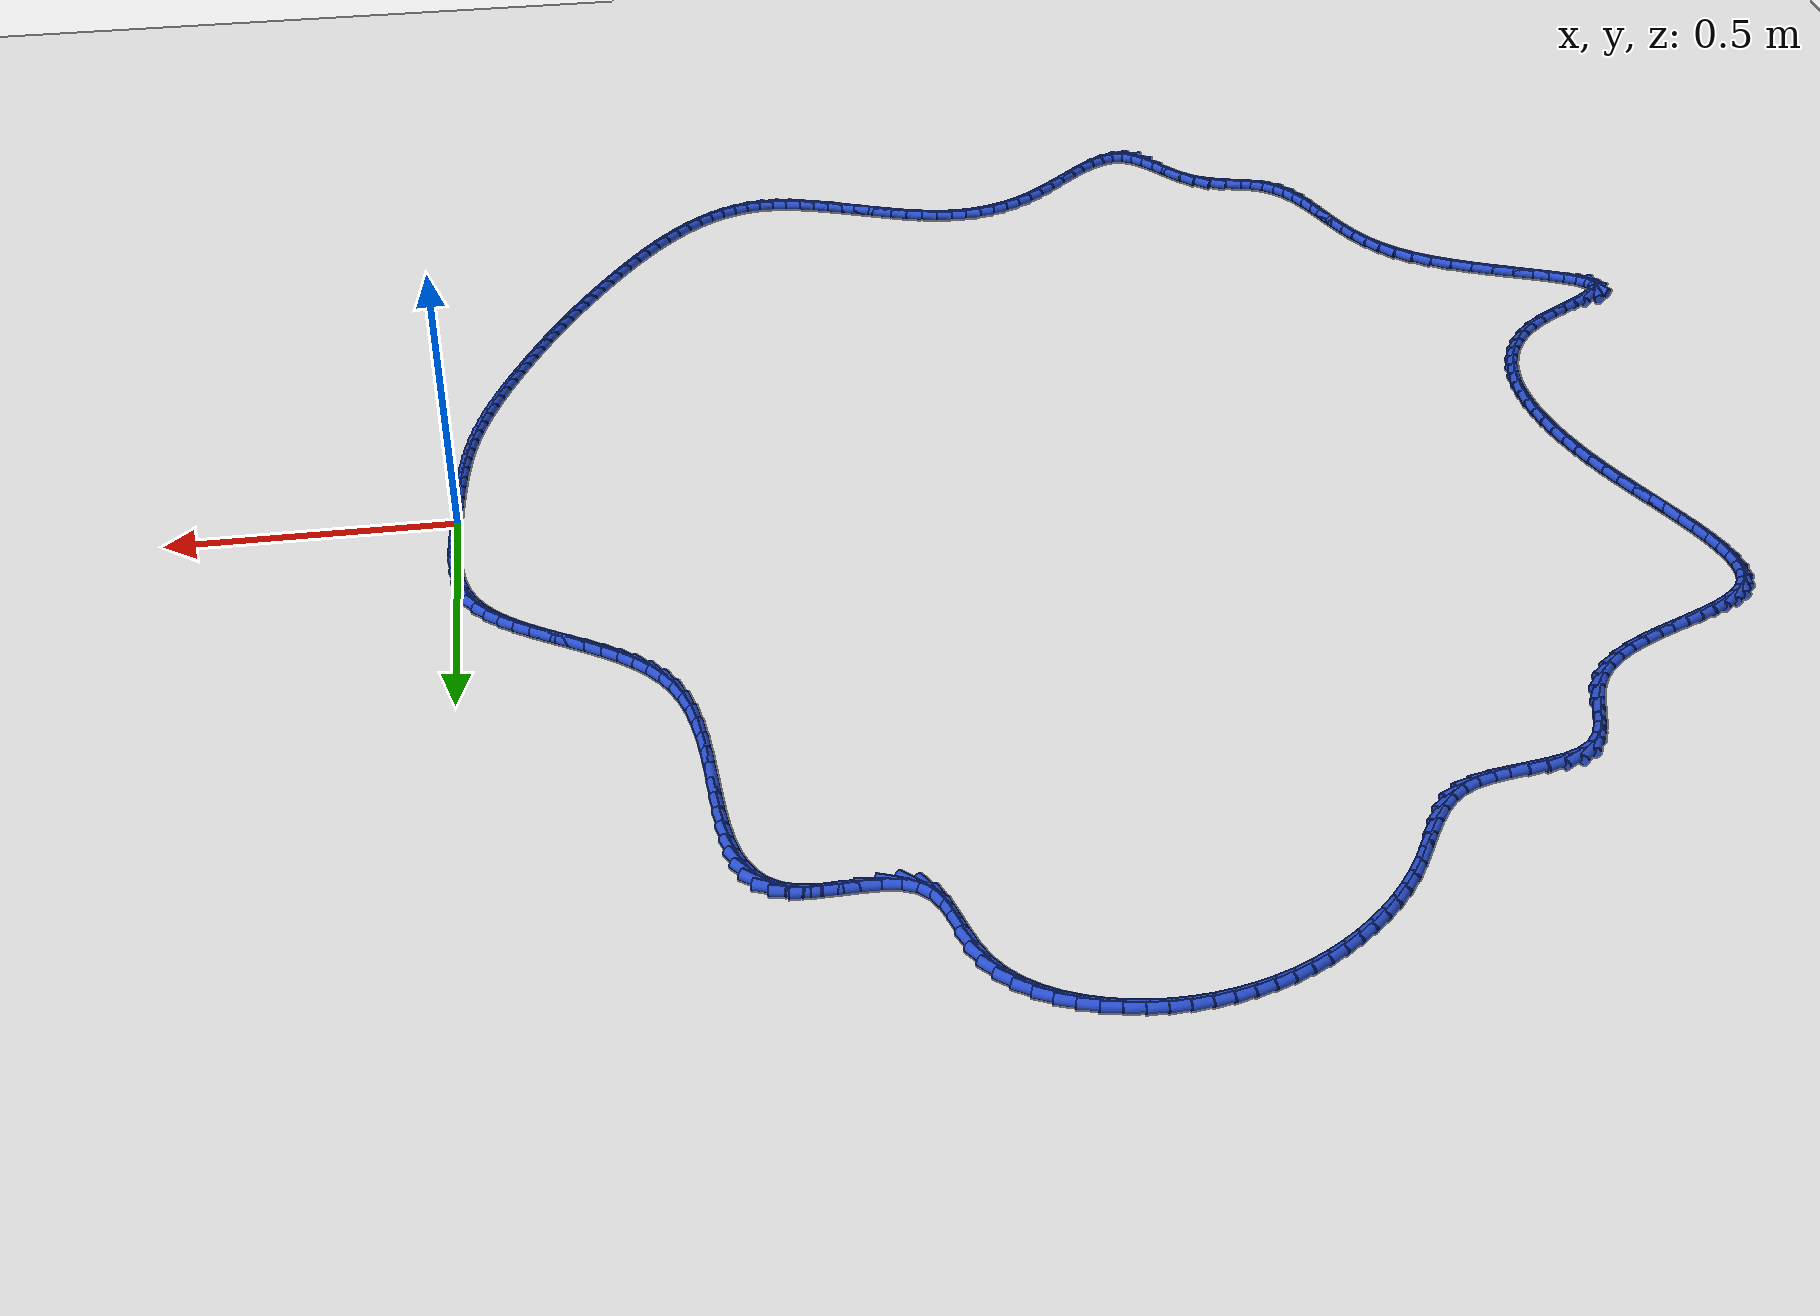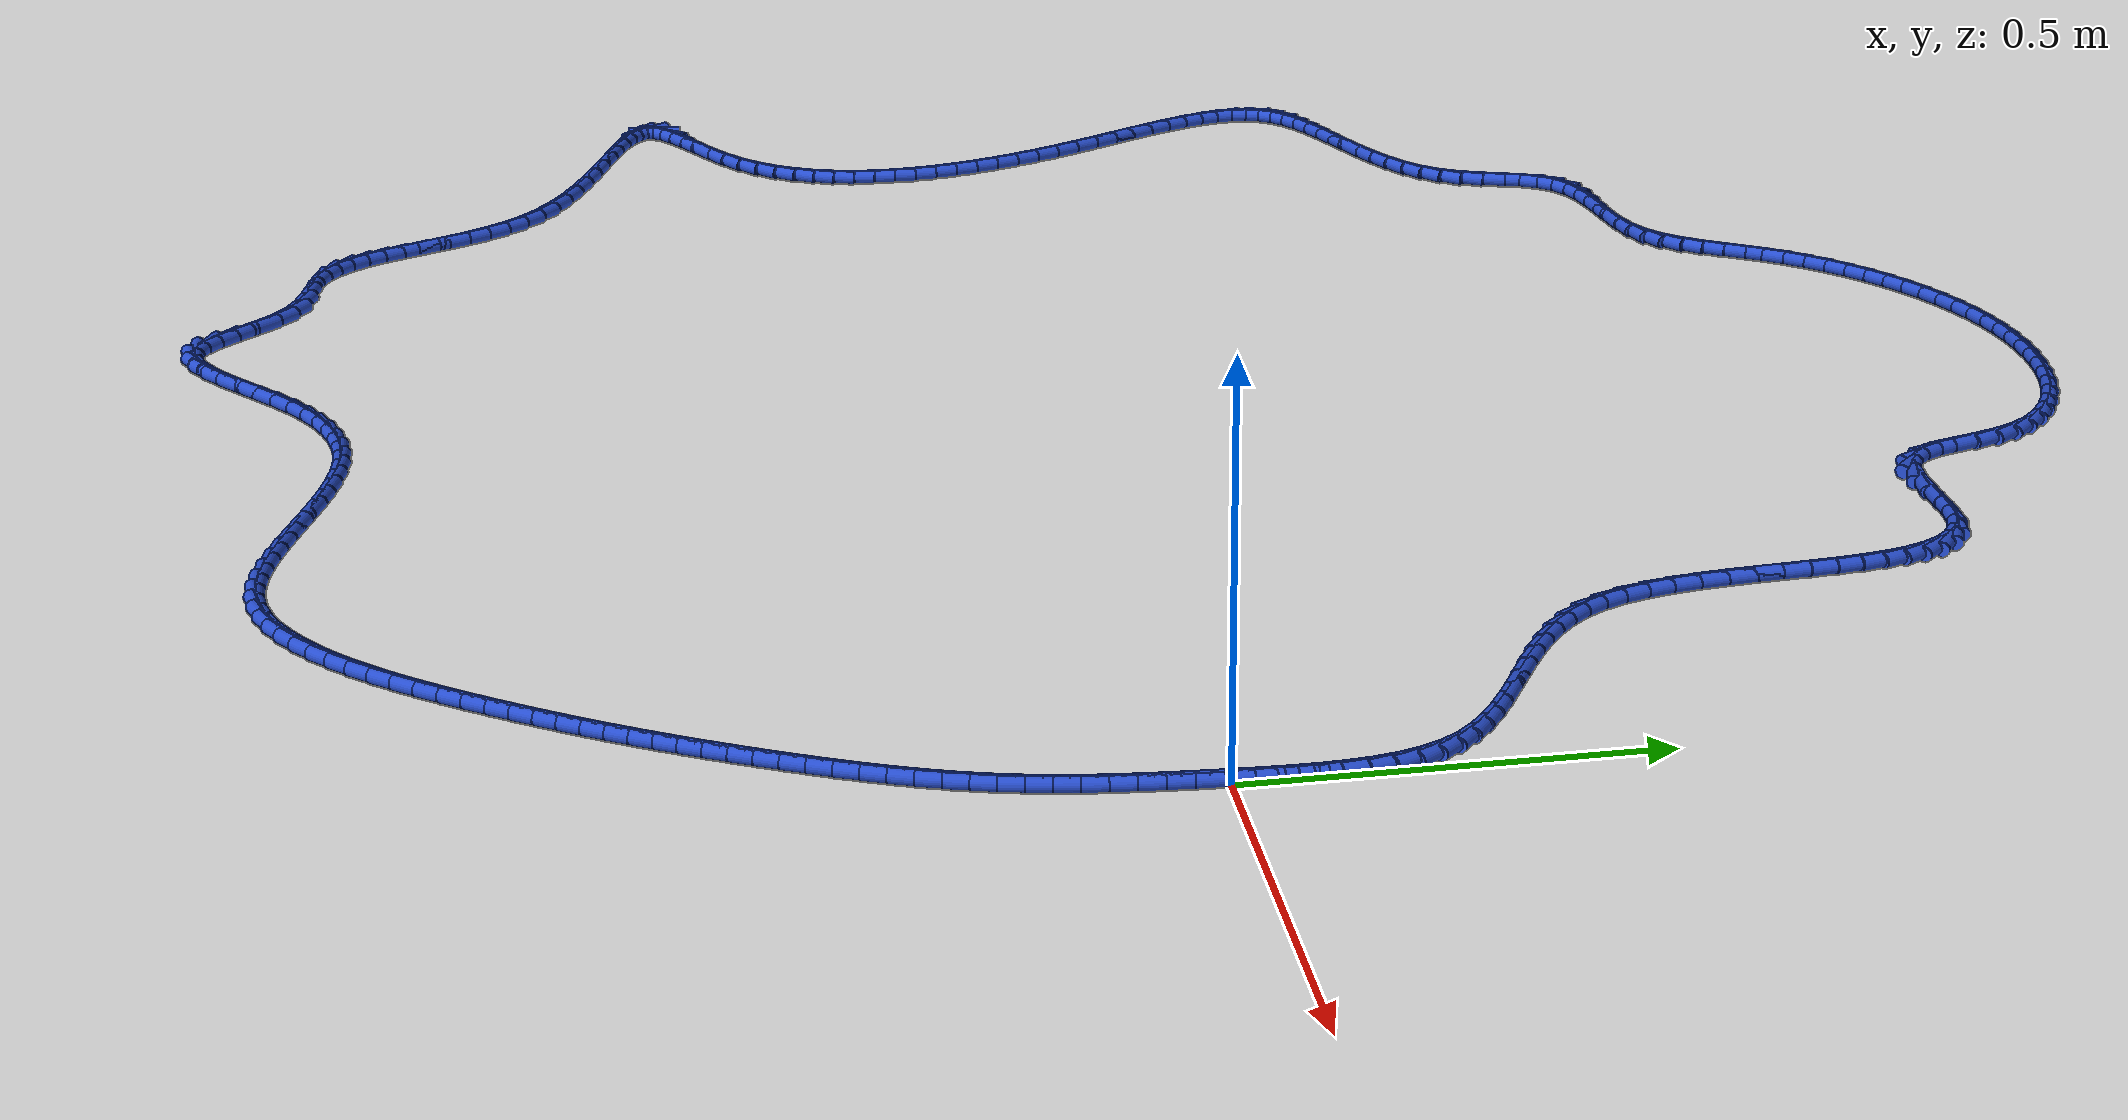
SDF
<sdf version="1.6">
 <world name="default">
  <light name="sun" type="directional">
   <pose>0 0 10 0 -0 0</pose>
   <diffuse>0.8 0.8 0.8 1</diffuse>
   <specular>0.2 0.2 0.2 1</specular>
   <attenuation>
    <range>1000</range>
    <constant>0.9</constant>
    <linear>0.01</linear>
    <quadratic>0.001</quadratic>
   </attenuation>
   <direction>-0.5 0.1 -0.9</direction>
  </light>
  <model name="ground_plane">
   <static>1</static>
   <link name="link">
    <collision name="collision">
     <geometry><plane><normal>0 0 1</normal><size>100 100</size></plane></geometry>
     <surface><friction><ode><mu>100</mu><mu2>50</mu2></ode></friction></surface>
    </collision>
    <visual name="visual">
     <cast_shadows>0</cast_shadows>
     <geometry><plane><normal>0 0 1</normal><size>100 100</size></plane></geometry>
     <material>
      <script><uri>file://media/materials/scripts/gazebo.material</uri><name>Gazebo/WhiteGlow</name></script>
     </material>
    </visual>
   </link>
  </model>
  <gravity>0 0 -9.8</gravity>
  <magnetic_field>6e-06 2.3e-05 -4.2e-05</magnetic_field>
  <atmosphere type="adiabatic"/>
  <physics name="default_physics" default="0" type="ode">
   <max_step_size>0.001</max_step_size>
   <real_time_factor>1</real_time_factor>
   <real_time_update_rate>1000</real_time_update_rate>
  </physics>
  <scene><ambient>0.4 0.4 0.4 1</ambient><background>0.7 0.7 0.7 1</background><shadows>1</shadows></scene>
  <spherical_coordinates>
   <surface_model>EARTH_WGS84</surface_model>
   <latitude_deg>0</latitude_deg>
   <longitude_deg>0</longitude_deg>
   <elevation>0</elevation>
   <heading_deg>0</heading_deg>
  </spherical_coordinates>
  <model name="line">
   <link name="link_0">
    <pose>-5.204170427930421e-18 4.163336342344337e-17 0.01 0 1.57 1.5197245684614573</pose>
    <collision name="collision">
     <geometry><cylinder><radius>0.01</radius><length>0.08</length></cylinder></geometry>
    </collision>
    <visual name="visual">
     <material>
      <script><name>Gazebo/Blue</name><uri>file://media/materials/scripts/gazebo.material</uri></script>
     </material>
     <geometry><cylinder><radius>0.01</radius><length>0.08</length></cylinder></geometry>
    </visual>
   </link>
   <link name="link_1">
    <pose>0.0016297047634209454 0.03188234823221027 0.01 0 1.57 1.5369050830865814</pose>
    <collision name="collision">
     <geometry><cylinder><radius>0.01</radius><length>0.08</length></cylinder></geometry>
    </collision>
    <visual name="visual">
     <material>
      <script><name>Gazebo/Blue</name><uri>file://media/materials/scripts/gazebo.material</uri></script>
     </material>
     <geometry><cylinder><radius>0.01</radius><length>0.08</length></cylinder></geometry>
    </visual>
   </link>
   <link name="link_2">
    <pose>0.0027185940531616274 0.06399897286291034 0.01 0 1.57 1.567410280789605</pose>
    <collision name="collision">
     <geometry><cylinder><radius>0.01</radius><length>0.08</length></cylinder></geometry>
    </collision>
    <visual name="visual">
     <material>
      <script><name>Gazebo/Blue</name><uri>file://media/materials/scripts/gazebo.material</uri></script>
     </material>
     <geometry><cylinder><radius>0.01</radius><length>0.08</length></cylinder></geometry>
    </visual>
   </link>
   <link name="link_3">
    <pose>0.002826859336559397 0.09597280590101473 0.01 0 1.57 -1.5291034431454884</pose>
    <collision name="collision">
     <geometry><cylinder><radius>0.01</radius><length>0.08</length></cylinder></geometry>
    </collision>
    <visual name="visual">
     <material>
      <script><name>Gazebo/Blue</name><uri>file://media/materials/scripts/gazebo.material</uri></script>
     </material>
     <geometry><cylinder><radius>0.01</radius><length>0.08</length></cylinder></geometry>
    </visual>
   </link>
   <link name="link_4">
    <pose>0.0015146920809516132 0.1274267793554381 0.01 0 1.57 -1.4673477267837867</pose>
    <collision name="collision">
     <geometry><cylinder><radius>0.01</radius><length>0.08</length></cylinder></geometry>
    </collision>
    <visual name="visual">
     <material>
      <script><name>Gazebo/Blue</name><uri>file://media/materials/scripts/gazebo.material</uri></script>
     </material>
     <geometry><cylinder><radius>0.01</radius><length>0.08</length></cylinder></geometry>
    </visual>
   </link>
   <link name="link_5">
    <pose>-0.0016577162463243672 0.1579838252350949 0.01 0 1.57 -1.3860460183805976</pose>
    <collision name="collision">
     <geometry><cylinder><radius>0.01</radius><length>0.08</length></cylinder></geometry>
    </collision>
    <visual name="visual">
     <material>
      <script><name>Gazebo/Blue</name><uri>file://media/materials/scripts/gazebo.material</uri></script>
     </material>
     <geometry><cylinder><radius>0.01</radius><length>0.08</length></cylinder></geometry>
    </visual>
   </link>
   <link name="link_6">
    <pose>-0.007130174177931185 0.18726687554889968 0.01 0 1.57 -1.281907335555164</pose>
    <collision name="collision">
     <geometry><cylinder><radius>0.01</radius><length>0.08</length></cylinder></geometry>
    </collision>
    <visual name="visual">
     <material>
      <script><name>Gazebo/Blue</name><uri>file://media/materials/scripts/gazebo.material</uri></script>
     </material>
     <geometry><cylinder><radius>0.01</radius><length>0.08</length></cylinder></geometry>
    </visual>
   </link>
   <link name="link_7">
    <pose>-0.015342490246531485 0.21489886230576702 0.01 0 1.57 -1.1521646684753741</pose>
    <collision name="collision">
     <geometry><cylinder><radius>0.01</radius><length>0.08</length></cylinder></geometry>
    </collision>
    <visual name="visual">
     <material>
      <script><name>Gazebo/Blue</name><uri>file://media/materials/scripts/gazebo.material</uri></script>
     </material>
     <geometry><cylinder><radius>0.01</radius><length>0.08</length></cylinder></geometry>
    </visual>
   </link>
   <link name="link_8">
    <pose>-0.026734472984787913 0.24050271751461139 0.01 0 1.57 -0.9986588103412112</pose>
    <collision name="collision">
     <geometry><cylinder><radius>0.01</radius><length>0.08</length></cylinder></geometry>
    </collision>
    <visual name="visual">
     <material>
      <script><name>Gazebo/Blue</name><uri>file://media/materials/scripts/gazebo.material</uri></script>
     </material>
     <geometry><cylinder><radius>0.01</radius><length>0.08</length></cylinder></geometry>
    </visual>
   </link>
   <link name="link_9">
    <pose>-0.04169859572575505 0.26373935189920267 0.01 0 1.57 -0.8518726115012331</pose>
    <collision name="collision">
     <geometry><cylinder><radius>0.01</radius><length>0.08</length></cylinder></geometry>
    </collision>
    <visual name="visual">
     <material>
      <script><name>Gazebo/Blue</name><uri>file://media/materials/scripts/gazebo.material</uri></script>
     </material>
     <geometry><cylinder><radius>0.01</radius><length>0.08</length></cylinder></geometry>
    </visual>
   </link>
   <link name="link_10">
    <pose>-0.06006258130907506 0.28472279559827457 0.01 0 1.57 -0.7339603214715237</pose>
    <collision name="collision">
     <geometry><cylinder><radius>0.01</radius><length>0.08</length></cylinder></geometry>
    </collision>
    <visual name="visual">
     <material>
      <script><name>Gazebo/Blue</name><uri>file://media/materials/scripts/gazebo.material</uri></script>
     </material>
     <geometry><cylinder><radius>0.01</radius><length>0.08</length></cylinder></geometry>
    </visual>
   </link>
   <link name="link_11">
    <pose>-0.08128280236514089 0.3038650262362648 0.01 0 1.57 -0.6454970557292256</pose>
    <collision name="collision">
     <geometry><cylinder><radius>0.01</radius><length>0.08</length></cylinder></geometry>
    </collision>
    <visual name="visual">
     <material>
      <script><name>Gazebo/Blue</name><uri>file://media/materials/scripts/gazebo.material</uri></script>
     </material>
     <geometry><cylinder><radius>0.01</radius><length>0.08</length></cylinder></geometry>
    </visual>
   </link>
   <link name="link_12">
    <pose>-0.10480912035673637 0.3215832455790542 0.01 0 1.57 -0.5840644457928118</pose>
    <collision name="collision">
     <geometry><cylinder><radius>0.01</radius><length>0.08</length></cylinder></geometry>
    </collision>
    <visual name="visual">
     <material>
      <script><name>Gazebo/Blue</name><uri>file://media/materials/scripts/gazebo.material</uri></script>
     </material>
     <geometry><cylinder><radius>0.01</radius><length>0.08</length></cylinder></geometry>
    </visual>
   </link>
   <link name="link_13">
    <pose>-0.1300913967466453 0.3382946553925232 0.01 0 1.57 -0.5467506337242448</pose>
    <collision name="collision">
     <geometry><cylinder><radius>0.01</radius><length>0.08</length></cylinder></geometry>
    </collision>
    <visual name="visual">
     <material>
      <script><name>Gazebo/Blue</name><uri>file://media/materials/scripts/gazebo.material</uri></script>
     </material>
     <geometry><cylinder><radius>0.01</radius><length>0.08</length></cylinder></geometry>
    </visual>
   </link>
   <link name="link_14">
    <pose>-0.15657949299765136 0.3544164574425528 0.01 0 1.57 -0.5312440793245494</pose>
    <collision name="collision">
     <geometry><cylinder><radius>0.01</radius><length>0.08</length></cylinder></geometry>
    </collision>
    <visual name="visual">
     <material>
      <script><name>Gazebo/Blue</name><uri>file://media/materials/scripts/gazebo.material</uri></script>
     </material>
     <geometry><cylinder><radius>0.01</radius><length>0.08</length></cylinder></geometry>
    </visual>
   </link>
   <link name="link_15">
    <pose>-0.1837232705725385 0.37036585349502343 0.01 0 1.57 -0.5362156325968038</pose>
    <collision name="collision">
     <geometry><cylinder><radius>0.01</radius><length>0.08</length></cylinder></geometry>
    </collision>
    <visual name="visual">
     <material>
      <script><name>Gazebo/Blue</name><uri>file://media/materials/scripts/gazebo.material</uri></script>
     </material>
     <geometry><cylinder><radius>0.01</radius><length>0.08</length></cylinder></geometry>
    </visual>
   </link>
   <link name="link_16">
    <pose>-0.2109725909340905 0.38656004531581606 0.01 0 1.57 -0.5613640888909666</pose>
    <collision name="collision">
     <geometry><cylinder><radius>0.01</radius><length>0.08</length></cylinder></geometry>
    </collision>
    <visual name="visual">
     <material>
      <script><name>Gazebo/Blue</name><uri>file://media/materials/scripts/gazebo.material</uri></script>
     </material>
     <geometry><cylinder><radius>0.01</radius><length>0.08</length></cylinder></geometry>
    </visual>
   </link>
   <link name="link_17">
    <pose>-0.2377773155450912 0.4034162346708114 0.01 0 1.57 -0.6072956276216246</pose>
    <collision name="collision">
     <geometry><cylinder><radius>0.01</radius><length>0.08</length></cylinder></geometry>
    </collision>
    <visual name="visual">
     <material>
      <script><name>Gazebo/Blue</name><uri>file://media/materials/scripts/gazebo.material</uri></script>
     </material>
     <geometry><cylinder><radius>0.01</radius><length>0.08</length></cylinder></geometry>
    </visual>
   </link>
   <link name="link_18">
    <pose>-0.2635873058683243 0.42135162332589005 0.01 0 1.57 -0.6752356784478661</pose>
    <collision name="collision">
     <geometry><cylinder><radius>0.01</radius><length>0.08</length></cylinder></geometry>
    </collision>
    <visual name="visual">
     <material>
      <script><name>Gazebo/Blue</name><uri>file://media/materials/scripts/gazebo.material</uri></script>
     </material>
     <geometry><cylinder><radius>0.01</radius><length>0.08</length></cylinder></geometry>
    </visual>
   </link>
   <link name="link_19">
    <pose>-0.2878524233665737 0.4407834130469327 0.01 0 1.57 -0.766448251580772</pose>
    <collision name="collision">
     <geometry><cylinder><radius>0.01</radius><length>0.08</length></cylinder></geometry>
    </collision>
    <visual name="visual">
     <material>
      <script><name>Gazebo/Blue</name><uri>file://media/materials/scripts/gazebo.material</uri></script>
     </material>
     <geometry><cylinder><radius>0.01</radius><length>0.08</length></cylinder></geometry>
    </visual>
   </link>
   <link name="link_20">
    <pose>-0.31002252950262316 0.46212880559982034 0.01 0 1.57 -0.8811950141061291</pose>
    <collision name="collision">
     <geometry><cylinder><radius>0.01</radius><length>0.08</length></cylinder></geometry>
    </collision>
    <visual name="visual">
     <material>
      <script><name>Gazebo/Blue</name><uri>file://media/materials/scripts/gazebo.material</uri></script>
     </material>
     <geometry><cylinder><radius>0.01</radius><length>0.08</length></cylinder></geometry>
    </visual>
   </link>
   <link name="link_21">
    <pose>-0.32954748573925646 0.4858050027504334 0.01 0 1.57 -1.017122977381416</pose>
    <collision name="collision">
     <geometry><cylinder><radius>0.01</radius><length>0.08</length></cylinder></geometry>
    </collision>
    <visual name="visual">
     <material>
      <script><name>Gazebo/Blue</name><uri>file://media/materials/scripts/gazebo.material</uri></script>
     </material>
     <geometry><cylinder><radius>0.01</radius><length>0.08</length></cylinder></geometry>
    </visual>
   </link>
   <link name="link_22">
    <pose>-0.34588039780600555 0.5122263608968104 0.01 0 1.57 -1.1549507821745515</pose>
    <collision name="collision">
     <geometry><cylinder><radius>0.01</radius><length>0.08</length></cylinder></geometry>
    </collision>
    <visual name="visual">
     <material>
      <script><name>Gazebo/Blue</name><uri>file://media/materials/scripts/gazebo.material</uri></script>
     </material>
     <geometry><cylinder><radius>0.01</radius><length>0.08</length></cylinder></geometry>
    </visual>
   </link>
   <link name="link_23">
    <pose>-0.35881236914581977 0.5415107972415587 0.01 0 1.57 -1.2667472253994232</pose>
    <collision name="collision">
     <geometry><cylinder><radius>0.01</radius><length>0.08</length></cylinder></geometry>
    </collision>
    <visual name="visual">
     <material>
      <script><name>Gazebo/Blue</name><uri>file://media/materials/scripts/gazebo.material</uri></script>
     </material>
     <geometry><cylinder><radius>0.01</radius><length>0.08</length></cylinder></geometry>
    </visual>
   </link>
   <link name="link_24">
    <pose>-0.3687634733122259 0.5732245939136491 0.01 0 1.57 -1.3526581128357738</pose>
    <collision name="collision">
     <geometry><cylinder><radius>0.01</radius><length>0.08</length></cylinder></geometry>
    </collision>
    <visual name="visual">
     <material>
      <script><name>Gazebo/Blue</name><uri>file://media/materials/scripts/gazebo.material</uri></script>
     </material>
     <geometry><cylinder><radius>0.01</radius><length>0.08</length></cylinder></geometry>
    </visual>
   </link>
   <link name="link_25">
    <pose>-0.37622235657713216 0.6068738916841132 0.01 0 1.57 -1.4165688702075998</pose>
    <collision name="collision">
     <geometry><cylinder><radius>0.01</radius><length>0.08</length></cylinder></geometry>
    </collision>
    <visual name="visual">
     <material>
      <script><name>Gazebo/Blue</name><uri>file://media/materials/scripts/gazebo.material</uri></script>
     </material>
     <geometry><cylinder><radius>0.01</radius><length>0.08</length></cylinder></geometry>
    </visual>
   </link>
   <link name="link_26">
    <pose>-0.3816776652124463 0.6419648313239825 0.01 0 1.57 -1.4618915231604726</pose>
    <collision name="collision">
     <geometry><cylinder><radius>0.01</radius><length>0.08</length></cylinder></geometry>
    </collision>
    <visual name="visual">
     <material>
      <script><name>Gazebo/Blue</name><uri>file://media/materials/scripts/gazebo.material</uri></script>
     </material>
     <geometry><cylinder><radius>0.01</radius><length>0.08</length></cylinder></geometry>
    </visual>
   </link>
   <link name="link_27">
    <pose>-0.38561804549007617 0.6780035536042887 0.01 0 1.57 -1.4911110204981752</pose>
    <collision name="collision">
     <geometry><cylinder><radius>0.01</radius><length>0.08</length></cylinder></geometry>
    </collision>
    <visual name="visual">
     <material>
      <script><name>Gazebo/Blue</name><uri>file://media/materials/scripts/gazebo.material</uri></script>
     </material>
     <geometry><cylinder><radius>0.01</radius><length>0.08</length></cylinder></geometry>
    </visual>
   </link>
   <link name="link_28">
    <pose>-0.3885321436819299 0.7144961992960633 0.01 0 1.57 -1.5056954279205166</pose>
    <collision name="collision">
     <geometry><cylinder><radius>0.01</radius><length>0.08</length></cylinder></geometry>
    </collision>
    <visual name="visual">
     <material>
      <script><name>Gazebo/Blue</name><uri>file://media/materials/scripts/gazebo.material</uri></script>
     </material>
     <geometry><cylinder><radius>0.01</radius><length>0.08</length></cylinder></geometry>
    </visual>
   </link>
   <link name="link_29">
    <pose>-0.3909086060599153 0.750948909170338 0.01 0 1.57 -1.5060888177872214</pose>
    <collision name="collision">
     <geometry><cylinder><radius>0.01</radius><length>0.08</length></cylinder></geometry>
    </collision>
    <visual name="visual">
     <material>
      <script><name>Gazebo/Blue</name><uri>file://media/materials/scripts/gazebo.material</uri></script>
     </material>
     <geometry><cylinder><radius>0.01</radius><length>0.08</length></cylinder></geometry>
    </visual>
   </link>
   <link name="link_30">
    <pose>-0.39323607889594026 0.7868678239981441 0.01 0 1.57 -1.4916547336572736</pose>
    <collision name="collision">
     <geometry><cylinder><radius>0.01</radius><length>0.08</length></cylinder></geometry>
    </collision>
    <visual name="visual">
     <material>
      <script><name>Gazebo/Blue</name><uri>file://media/materials/scripts/gazebo.material</uri></script>
     </material>
     <geometry><cylinder><radius>0.01</radius><length>0.08</length></cylinder></geometry>
    </visual>
   </link>
   <link name="link_31">
    <pose>-0.3960032084619128 0.8217590845505134 0.01 0 1.57 -1.4605037289413374</pose>
    <collision name="collision">
     <geometry><cylinder><radius>0.01</radius><length>0.08</length></cylinder></geometry>
    </collision>
    <visual name="visual">
     <material>
      <script><name>Gazebo/Blue</name><uri>file://media/materials/scripts/gazebo.material</uri></script>
     </material>
     <geometry><cylinder><radius>0.01</radius><length>0.08</length></cylinder></geometry>
    </visual>
   </link>
   <link name="link_32">
    <pose>-0.39969864102974073 0.8551288315984773 0.01 0 1.57 -1.4091670309096473</pose>
    <collision name="collision">
     <geometry><cylinder><radius>0.01</radius><length>0.08</length></cylinder></geometry>
    </collision>
    <visual name="visual">
     <material>
      <script><name>Gazebo/Blue</name><uri>file://media/materials/scripts/gazebo.material</uri></script>
     </material>
     <geometry><cylinder><radius>0.01</radius><length>0.08</length></cylinder></geometry>
    </visual>
   </link>
   <link name="link_33">
    <pose>-0.4048110228713321 0.8864832059130675 0.01 0 1.57 -1.3321349160981737</pose>
    <collision name="collision">
     <geometry><cylinder><radius>0.01</radius><length>0.08</length></cylinder></geometry>
    </collision>
    <visual name="visual">
     <material>
      <script><name>Gazebo/Blue</name><uri>file://media/materials/scripts/gazebo.material</uri></script>
     </material>
     <geometry><cylinder><radius>0.01</radius><length>0.08</length></cylinder></geometry>
    </visual>
   </link>
   <link name="link_34">
    <pose>-0.4118290002585948 0.9153283482653155 0.01 0 1.57 -1.2215090116597271</pose>
    <collision name="collision">
     <geometry><cylinder><radius>0.01</radius><length>0.08</length></cylinder></geometry>
    </collision>
    <visual name="visual">
     <material>
      <script><name>Gazebo/Blue</name><uri>file://media/materials/scripts/gazebo.material</uri></script>
     </material>
     <geometry><cylinder><radius>0.01</radius><length>0.08</length></cylinder></geometry>
    </visual>
   </link>
   <link name="link_35">
    <pose>-0.4212412194634367 0.9411703994262525 0.01 0 1.57 -1.0677709668213629</pose>
    <collision name="collision">
     <geometry><cylinder><radius>0.01</radius><length>0.08</length></cylinder></geometry>
    </collision>
    <visual name="visual">
     <material>
      <script><name>Gazebo/Blue</name><uri>file://media/materials/scripts/gazebo.material</uri></script>
     </material>
     <geometry><cylinder><radius>0.01</radius><length>0.08</length></cylinder></geometry>
    </visual>
   </link>
   <link name="link_36">
    <pose>-0.43353632675776577 0.9635155001669107 0.01 0 1.57 -0.8642343055578869</pose>
    <collision name="collision">
     <geometry><cylinder><radius>0.01</radius><length>0.08</length></cylinder></geometry>
    </collision>
    <visual name="visual">
     <material>
      <script><name>Gazebo/Blue</name><uri>file://media/materials/scripts/gazebo.material</uri></script>
     </material>
     <geometry><cylinder><radius>0.01</radius><length>0.08</length></cylinder></geometry>
    </visual>
   </link>
   <link name="link_37">
    <pose>-0.44920296841348983 0.9818697912583212 0.01 0 1.57 -0.6175957991414567</pose>
    <collision name="collision">
     <geometry><cylinder><radius>0.01</radius><length>0.08</length></cylinder></geometry>
    </collision>
    <visual name="visual">
     <material>
      <script><name>Gazebo/Blue</name><uri>file://media/materials/scripts/gazebo.material</uri></script>
     </material>
     <geometry><cylinder><radius>0.01</radius><length>0.08</length></cylinder></geometry>
    </visual>
   </link>
   <link name="link_38">
    <pose>-0.468729790702517 0.995739413471516 0.01 0 1.57 -0.3564820017984597</pose>
    <collision name="collision">
     <geometry><cylinder><radius>0.01</radius><length>0.08</length></cylinder></geometry>
    </collision>
    <visual name="visual">
     <material>
      <script><name>Gazebo/Blue</name><uri>file://media/materials/scripts/gazebo.material</uri></script>
     </material>
     <geometry><cylinder><radius>0.01</radius><length>0.08</length></cylinder></geometry>
    </visual>
   </link>
   <link name="link_39">
    <pose>-0.4926054398967551 1.004630507577526 0.01 0 1.57 -0.1285843808246256</pose>
    <collision name="collision">
     <geometry><cylinder><radius>0.01</radius><length>0.08</length></cylinder></geometry>
    </collision>
    <visual name="visual">
     <material>
      <script><name>Gazebo/Blue</name><uri>file://media/materials/scripts/gazebo.material</uri></script>
     </material>
     <geometry><cylinder><radius>0.01</radius><length>0.08</length></cylinder></geometry>
    </visual>
   </link>
   <link name="link_40">
    <pose>-0.5210911083533573 1.0083136409340643 0.01 0 1.57 -0.002757266186198285</pose>
    <collision name="collision">
     <geometry><cylinder><radius>0.01</radius><length>0.08</length></cylinder></geometry>
    </collision>
    <visual name="visual">
     <material>
      <script><name>Gazebo/Blue</name><uri>file://media/materials/scripts/gazebo.material</uri></script>
     </material>
     <geometry><cylinder><radius>0.01</radius><length>0.08</length></cylinder></geometry>
    </visual>
   </link>
   <link name="link_41">
    <pose>-0.5528636562597132 1.0084012465280636 0.01 0 1.57 0.03362024390669865</pose>
    <collision name="collision">
     <geometry><cylinder><radius>0.01</radius><length>0.08</length></cylinder></geometry>
    </collision>
    <visual name="visual">
     <material>
      <script><name>Gazebo/Blue</name><uri>file://media/materials/scripts/gazebo.material</uri></script>
     </material>
     <geometry><cylinder><radius>0.01</radius><length>0.08</length></cylinder></geometry>
    </visual>
   </link>
   <link name="link_42">
    <pose>-0.5859259888014531 1.0072892638465933 0.01 0 1.57 -0.0026967857543557204</pose>
    <collision name="collision">
     <geometry><cylinder><radius>0.01</radius><length>0.08</length></cylinder></geometry>
    </collision>
    <visual name="visual">
     <material>
      <script><name>Gazebo/Blue</name><uri>file://media/materials/scripts/gazebo.material</uri></script>
     </material>
     <geometry><cylinder><radius>0.01</radius><length>0.08</length></cylinder></geometry>
    </visual>
   </link>
   <link name="link_43">
    <pose>-0.6182785342259401 1.0073765119417197 0.01 0 1.57 -0.12368729279589362</pose>
    <collision name="collision">
     <geometry><cylinder><radius>0.01</radius><length>0.08</length></cylinder></geometry>
    </collision>
    <visual name="visual">
     <material>
      <script><name>Gazebo/Blue</name><uri>file://media/materials/scripts/gazebo.material</uri></script>
     </material>
     <geometry><cylinder><radius>0.01</radius><length>0.08</length></cylinder></geometry>
    </visual>
   </link>
   <link name="link_44">
    <pose>-0.6479217207805366 1.0110618098655089 0.01 0 1.57 -0.37038646269286063</pose>
    <collision name="collision">
     <geometry><cylinder><radius>0.01</radius><length>0.08</length></cylinder></geometry>
    </collision>
    <visual name="visual">
     <material>
      <script><name>Gazebo/Blue</name><uri>file://media/materials/scripts/gazebo.material</uri></script>
     </material>
     <geometry><cylinder><radius>0.01</radius><length>0.08</length></cylinder></geometry>
    </visual>
   </link>
   <link name="link_45">
    <pose>-0.6728559767126059 1.0207439766700275 0.01 0 1.57 -0.7573637008103862</pose>
    <collision name="collision">
     <geometry><cylinder><radius>0.01</radius><length>0.08</length></cylinder></geometry>
    </collision>
    <visual name="visual">
     <material>
      <script><name>Gazebo/Blue</name><uri>file://media/materials/scripts/gazebo.material</uri></script>
     </material>
     <geometry><cylinder><radius>0.01</radius><length>0.08</length></cylinder></geometry>
    </visual>
   </link>
   <link name="link_46">
    <pose>-0.691487210400188 1.038358805193856 0.01 0 1.57 -1.0710989841286964</pose>
    <collision name="collision">
     <geometry><cylinder><radius>0.01</radius><length>0.08</length></cylinder></geometry>
    </collision>
    <visual name="visual">
     <material>
      <script><name>Gazebo/Blue</name><uri>file://media/materials/scripts/gazebo.material</uri></script>
     </material>
     <geometry><cylinder><radius>0.01</radius><length>0.08</length></cylinder></geometry>
    </visual>
   </link>
   <link name="link_47">
    <pose>-0.7048511845557581 1.062839002791563 0.01 0 1.57 -1.2340177851394074</pose>
    <collision name="collision">
     <geometry><cylinder><radius>0.01</radius><length>0.08</length></cylinder></geometry>
    </collision>
    <visual name="visual">
     <material>
      <script><name>Gazebo/Blue</name><uri>file://media/materials/scripts/gazebo.material</uri></script>
     </material>
     <geometry><cylinder><radius>0.01</radius><length>0.08</length></cylinder></geometry>
    </visual>
   </link>
   <link name="link_48">
    <pose>-0.7150326963520536 1.0919193625003398 0.01 0 1.57 -1.2892133753180883</pose>
    <collision name="collision">
     <geometry><cylinder><radius>0.01</radius><length>0.08</length></cylinder></geometry>
    </collision>
    <visual name="visual">
     <material>
      <script><name>Gazebo/Blue</name><uri>file://media/materials/scripts/gazebo.material</uri></script>
     </material>
     <geometry><cylinder><radius>0.01</radius><length>0.08</length></cylinder></geometry>
    </visual>
   </link>
   <link name="link_49">
    <pose>-0.7241192705071197 1.1233315627165315 0.01 0 1.57 -1.2608936443983363</pose>
    <collision name="collision">
     <geometry><cylinder><radius>0.01</radius><length>0.08</length></cylinder></geometry>
    </collision>
    <visual name="visual">
     <material>
      <script><name>Gazebo/Blue</name><uri>file://media/materials/scripts/gazebo.material</uri></script>
     </material>
     <geometry><cylinder><radius>0.01</radius><length>0.08</length></cylinder></geometry>
    </visual>
   </link>
   <link name="link_50">
    <pose>-0.7341984317390019 1.1548072818364854 0.01 0 1.57 -1.1490006195326392</pose>
    <collision name="collision">
     <geometry><cylinder><radius>0.01</radius><length>0.08</length></cylinder></geometry>
    </collision>
    <visual name="visual">
     <material>
      <script><name>Gazebo/Blue</name><uri>file://media/materials/scripts/gazebo.material</uri></script>
     </material>
     <geometry><cylinder><radius>0.01</radius><length>0.08</length></cylinder></geometry>
    </visual>
   </link>
   <link name="link_51">
    <pose>-0.7473402795493991 1.1840941660274253 0.01 0 1.57 -0.9797933281670176</pose>
    <collision name="collision">
     <geometry><cylinder><radius>0.01</radius><length>0.08</length></cylinder></geometry>
    </collision>
    <visual name="visual">
     <material>
      <script><name>Gazebo/Blue</name><uri>file://media/materials/scripts/gazebo.material</uri></script>
     </material>
     <geometry><cylinder><radius>0.01</radius><length>0.08</length></cylinder></geometry>
    </visual>
   </link>
   <link name="link_52">
    <pose>-0.7646223096916805 1.209849443806087 0.01 0 1.57 -0.8148135316992393</pose>
    <collision name="collision">
     <geometry><cylinder><radius>0.01</radius><length>0.08</length></cylinder></geometry>
    </collision>
    <visual name="visual">
     <material>
      <script><name>Gazebo/Blue</name><uri>file://media/materials/scripts/gazebo.material</uri></script>
     </material>
     <geometry><cylinder><radius>0.01</radius><length>0.08</length></cylinder></geometry>
    </visual>
   </link>
   <link name="link_53">
    <pose>-0.7856131574820419 1.2321130030070255 0.01 0 1.57 -0.6649157038926824</pose>
    <collision name="collision">
     <geometry><cylinder><radius>0.01</radius><length>0.08</length></cylinder></geometry>
    </collision>
    <visual name="visual">
     <material>
      <script><name>Gazebo/Blue</name><uri>file://media/materials/scripts/gazebo.material</uri></script>
     </material>
     <geometry><cylinder><radius>0.01</radius><length>0.08</length></cylinder></geometry>
    </visual>
   </link>
   <link name="link_54">
    <pose>-0.8097550712528764 1.2510405474385604 0.01 0 1.57 -0.5322971140219566</pose>
    <collision name="collision">
     <geometry><cylinder><radius>0.01</radius><length>0.08</length></cylinder></geometry>
    </collision>
    <visual name="visual">
     <material>
      <script><name>Gazebo/Blue</name><uri>file://media/materials/scripts/gazebo.material</uri></script>
     </material>
     <geometry><cylinder><radius>0.01</radius><length>0.08</length></cylinder></geometry>
    </visual>
   </link>
   <link name="link_55">
    <pose>-0.836490299336578 1.2667877809090107 0.01 0 1.57 -0.4163538527721515</pose>
    <collision name="collision">
     <geometry><cylinder><radius>0.01</radius><length>0.08</length></cylinder></geometry>
    </collision>
    <visual name="visual">
     <material>
      <script><name>Gazebo/Blue</name><uri>file://media/materials/scripts/gazebo.material</uri></script>
     </material>
     <geometry><cylinder><radius>0.01</radius><length>0.08</length></cylinder></geometry>
    </visual>
   </link>
   <link name="link_56">
    <pose>-0.86526109006554 1.2795104072266952 0.01 0 1.57 -0.31491730079808405</pose>
    <collision name="collision">
     <geometry><cylinder><radius>0.01</radius><length>0.08</length></cylinder></geometry>
    </collision>
    <visual name="visual">
     <material>
      <script><name>Gazebo/Blue</name><uri>file://media/materials/scripts/gazebo.material</uri></script>
     </material>
     <geometry><cylinder><radius>0.01</radius><length>0.08</length></cylinder></geometry>
    </visual>
   </link>
   <link name="link_57">
    <pose>-0.8955096917721564 1.289364130199933 0.01 0 1.57 -0.22520682919508236</pose>
    <collision name="collision">
     <geometry><cylinder><radius>0.01</radius><length>0.08</length></cylinder></geometry>
    </collision>
    <visual name="visual">
     <material>
      <script><name>Gazebo/Blue</name><uri>file://media/materials/scripts/gazebo.material</uri></script>
     </material>
     <geometry><cylinder><radius>0.01</radius><length>0.08</length></cylinder></geometry>
    </visual>
   </link>
   <link name="link_58">
    <pose>-0.9266783527888204 1.2965046536370426 0.01 0 1.57 -0.1442617764112294</pose>
    <collision name="collision">
     <geometry><cylinder><radius>0.01</radius><length>0.08</length></cylinder></geometry>
    </collision>
    <visual name="visual">
     <material>
      <script><name>Gazebo/Blue</name><uri>file://media/materials/scripts/gazebo.material</uri></script>
     </material>
     <geometry><cylinder><radius>0.01</radius><length>0.08</length></cylinder></geometry>
    </visual>
   </link>
   <link name="link_59">
    <pose>-0.9582171342124489 1.301086322193884 0.01 0 1.57 -0.06770821401263062</pose>
    <collision name="collision">
     <geometry><cylinder><radius>0.01</radius><length>0.08</length></cylinder></geometry>
    </collision>
    <visual name="visual">
     <material>
      <script><name>Gazebo/Blue</name><uri>file://media/materials/scripts/gazebo.material</uri></script>
     </material>
     <geometry><cylinder><radius>0.01</radius><length>0.08</length></cylinder></geometry>
    </visual>
   </link>
   <link name="link_60">
    <pose>-0.9897855805461712 1.3032270376147213 0.01 0 1.57 0.00704809466019418</pose>
    <collision name="collision">
     <geometry><cylinder><radius>0.01</radius><length>0.08</length></cylinder></geometry>
    </collision>
    <visual name="visual">
     <material>
      <script><name>Gazebo/Blue</name><uri>file://media/materials/scripts/gazebo.material</uri></script>
     </material>
     <geometry><cylinder><radius>0.01</radius><length>0.08</length></cylinder></geometry>
    </visual>
   </link>
   <link name="link_61">
    <pose>-1.0212707415783326 1.3030051235447886 0.01 0 1.57 0.07996266134254679</pose>
    <collision name="collision">
     <geometry><cylinder><radius>0.01</radius><length>0.08</length></cylinder></geometry>
    </collision>
    <visual name="visual">
     <material>
      <script><name>Gazebo/Blue</name><uri>file://media/materials/scripts/gazebo.material</uri></script>
     </material>
     <geometry><cylinder><radius>0.01</radius><length>0.08</length></cylinder></geometry>
    </visual>
   </link>
   <link name="link_62">
    <pose>-1.0525710919351297 1.3004969161002675 0.01 0 1.57 0.1509725087594473</pose>
    <collision name="collision">
     <geometry><cylinder><radius>0.01</radius><length>0.08</length></cylinder></geometry>
    </collision>
    <visual name="visual">
     <material>
      <script><name>Gazebo/Blue</name><uri>file://media/materials/scripts/gazebo.material</uri></script>
     </material>
     <geometry><cylinder><radius>0.01</radius><length>0.08</length></cylinder></geometry>
    </visual>
   </link>
   <link name="link_63">
    <pose>-1.083585106242758 1.29577875139734 0.01 0 1.57 0.22009898686347276</pose>
    <collision name="collision">
     <geometry><cylinder><radius>0.01</radius><length>0.08</length></cylinder></geometry>
    </collision>
    <visual name="visual">
     <material>
      <script><name>Gazebo/Blue</name><uri>file://media/materials/scripts/gazebo.material</uri></script>
     </material>
     <geometry><cylinder><radius>0.01</radius><length>0.08</length></cylinder></geometry>
    </visual>
   </link>
   <link name="link_64">
    <pose>-1.114211259127414 1.288926965552187 0.01 0 1.57 0.2874348406376471</pose>
    <collision name="collision">
     <geometry><cylinder><radius>0.01</radius><length>0.08</length></cylinder></geometry>
    </collision>
    <visual name="visual">
     <material>
      <script><name>Gazebo/Blue</name><uri>file://media/materials/scripts/gazebo.material</uri></script>
     </material>
     <geometry><cylinder><radius>0.01</radius><length>0.08</length></cylinder></geometry>
    </visual>
   </link>
   <link name="link_65">
    <pose>-1.1443480252152947 1.2800178946809913 0.01 0 1.57 0.3531305983465164</pose>
    <collision name="collision">
     <geometry><cylinder><radius>0.01</radius><length>0.08</length></cylinder></geometry>
    </collision>
    <visual name="visual">
     <material>
      <script><name>Gazebo/Blue</name><uri>file://media/materials/scripts/gazebo.material</uri></script>
     </material>
     <geometry><cylinder><radius>0.01</radius><length>0.08</length></cylinder></geometry>
    </visual>
   </link>
   <link name="link_66">
    <pose>-1.1738938791325955 1.2691278748999342 0.01 0 1.57 0.41738159373105677</pose>
    <collision name="collision">
     <geometry><cylinder><radius>0.01</radius><length>0.08</length></cylinder></geometry>
    </collision>
    <visual name="visual">
     <material>
      <script><name>Gazebo/Blue</name><uri>file://media/materials/scripts/gazebo.material</uri></script>
     </material>
     <geometry><cylinder><radius>0.01</radius><length>0.08</length></cylinder></geometry>
    </visual>
   </link>
   <link name="link_67">
    <pose>-1.202747295505513 1.256333242325197 0.01 0 1.57 0.4804163875431029</pose>
    <collision name="collision">
     <geometry><cylinder><radius>0.01</radius><length>0.08</length></cylinder></geometry>
    </collision>
    <visual name="visual">
     <material>
      <script><name>Gazebo/Blue</name><uri>file://media/materials/scripts/gazebo.material</uri></script>
     </material>
     <geometry><cylinder><radius>0.01</radius><length>0.08</length></cylinder></geometry>
    </visual>
   </link>
   <link name="link_68">
    <pose>-1.230806748960243 1.2417103330729615 0.01 0 1.57 0.5424868950441456</pose>
    <collision name="collision">
     <geometry><cylinder><radius>0.01</radius><length>0.08</length></cylinder></geometry>
    </collision>
    <visual name="visual">
     <material>
      <script><name>Gazebo/Blue</name><uri>file://media/materials/scripts/gazebo.material</uri></script>
     </material>
     <geometry><cylinder><radius>0.01</radius><length>0.08</length></cylinder></geometry>
    </visual>
   </link>
   <link name="link_69">
    <pose>-1.2579707141229823 1.2253354832594094 0.01 0 1.57 0.6038601906437397</pose>
    <collision name="collision">
     <geometry><cylinder><radius>0.01</radius><length>0.08</length></cylinder></geometry>
    </collision>
    <visual name="visual">
     <material>
      <script><name>Gazebo/Blue</name><uri>file://media/materials/scripts/gazebo.material</uri></script>
     </material>
     <geometry><cylinder><radius>0.01</radius><length>0.08</length></cylinder></geometry>
    </visual>
   </link>
   <link name="link_70">
    <pose>-1.2841376656199275 1.2072850290007229 0.01 0 1.57 0.6648117430324205</pose>
    <collision name="collision">
     <geometry><cylinder><radius>0.01</radius><length>0.08</length></cylinder></geometry>
    </collision>
    <visual name="visual">
     <material>
      <script><name>Gazebo/Blue</name><uri>file://media/materials/scripts/gazebo.material</uri></script>
     </material>
     <geometry><cylinder><radius>0.01</radius><length>0.08</length></cylinder></geometry>
    </visual>
   </link>
   <link name="link_71">
    <pose>-1.3092060780772743 1.187635306413083 0.01 0 1.57 0.7256197099627612</pose>
    <collision name="collision">
     <geometry><cylinder><radius>0.01</radius><length>0.08</length></cylinder></geometry>
    </collision>
    <visual name="visual">
     <material>
      <script><name>Gazebo/Blue</name><uri>file://media/materials/scripts/gazebo.material</uri></script>
     </material>
     <geometry><cylinder><radius>0.01</radius><length>0.08</length></cylinder></geometry>
    </visual>
   </link>
   <link name="link_72">
    <pose>-1.3330744261212186 1.1664626516126715 0.01 0 1.57 0.786559864057263</pose>
    <collision name="collision">
     <geometry><cylinder><radius>0.01</radius><length>0.08</length></cylinder></geometry>
    </collision>
    <visual name="visual">
     <material>
      <script><name>Gazebo/Blue</name><uri>file://media/materials/scripts/gazebo.material</uri></script>
     </material>
     <geometry><cylinder><radius>0.01</radius><length>0.08</length></cylinder></geometry>
    </visual>
   </link>
   <link name="link_73">
    <pose>-1.3556411843779574 1.1438434007156706 0.01 0 1.57 0.8479007077315786</pose>
    <collision name="collision">
     <geometry><cylinder><radius>0.01</radius><length>0.08</length></cylinder></geometry>
    </collision>
    <visual name="visual">
     <material>
      <script><name>Gazebo/Blue</name><uri>file://media/materials/scripts/gazebo.material</uri></script>
     </material>
     <geometry><cylinder><radius>0.01</radius><length>0.08</length></cylinder></geometry>
    </visual>
   </link>
   <link name="link_74">
    <pose>-1.3768048274736868 1.1198538898382613 0.01 0 1.57 0.909898353398594</pose>
    <collision name="collision">
     <geometry><cylinder><radius>0.01</radius><length>0.08</length></cylinder></geometry>
    </collision>
    <visual name="visual">
     <material>
      <script><name>Gazebo/Blue</name><uri>file://media/materials/scripts/gazebo.material</uri></script>
     </material>
     <geometry><cylinder><radius>0.01</radius><length>0.08</length></cylinder></geometry>
    </visual>
   </link>
   <link name="link_75">
    <pose>-1.396463830034603 1.094570455096626 0.01 0 1.57 0.9727851141280072</pose>
    <collision name="collision">
     <geometry><cylinder><radius>0.01</radius><length>0.08</length></cylinder></geometry>
    </collision>
    <visual name="visual">
     <material>
      <script><name>Gazebo/Blue</name><uri>file://media/materials/scripts/gazebo.material</uri></script>
     </material>
     <geometry><cylinder><radius>0.01</radius><length>0.08</length></cylinder></geometry>
    </visual>
   </link>
   <link name="link_76">
    <pose>-1.4145168040193807 1.0680695543337722 0.01 0 1.57 1.027722597651463</pose>
    <collision name="collision">
     <geometry><cylinder><radius>0.01</radius><length>0.08</length></cylinder></geometry>
    </collision>
    <visual name="visual">
     <material>
      <script><name>Gazebo/Blue</name><uri>file://media/materials/scripts/gazebo.material</uri></script>
     </material>
     <geometry><cylinder><radius>0.01</radius><length>0.08</length></cylinder></geometry>
    </visual>
   </link>
   <link name="link_77">
    <pose>-1.431083548650256 1.0406236982420816 0.01 0 1.57 1.0477477935533854</pose>
    <collision name="collision">
     <geometry><cylinder><radius>0.01</radius><length>0.08</length></cylinder></geometry>
    </collision>
    <visual name="visual">
     <material>
      <script><name>Gazebo/Blue</name><uri>file://media/materials/scripts/gazebo.material</uri></script>
     </material>
     <geometry><cylinder><radius>0.01</radius><length>0.08</length></cylinder></geometry>
    </visual>
   </link>
   <link name="link_78">
    <pose>-1.4469543520123456 1.0130996959826772 0.01 0 1.57 1.027129079480465</pose>
    <collision name="collision">
     <geometry><cylinder><radius>0.01</radius><length>0.08</length></cylinder></geometry>
    </collision>
    <visual name="visual">
     <material>
      <script><name>Gazebo/Blue</name><uri>file://media/materials/scripts/gazebo.material</uri></script>
     </material>
     <geometry><cylinder><radius>0.01</radius><length>0.08</length></cylinder></geometry>
    </visual>
   </link>
   <link name="link_79">
    <pose>-1.4630460681201318 0.9864765404413977 0.01 0 1.57 0.9625385239471408</pose>
    <collision name="collision">
     <geometry><cylinder><radius>0.01</radius><length>0.08</length></cylinder></geometry>
    </collision>
    <visual name="visual">
     <material>
      <script><name>Gazebo/Blue</name><uri>file://media/materials/scripts/gazebo.material</uri></script>
     </material>
     <geometry><cylinder><radius>0.01</radius><length>0.08</length></cylinder></geometry>
    </visual>
   </link>
   <link name="link_80">
    <pose>-1.480275550988097 0.9617332245040802 0.01 0 1.57 0.8484785357665837</pose>
    <collision name="collision">
     <geometry><cylinder><radius>0.01</radius><length>0.08</length></cylinder></geometry>
    </collision>
    <visual name="visual">
     <material>
      <script><name>Gazebo/Blue</name><uri>file://media/materials/scripts/gazebo.material</uri></script>
     </material>
     <geometry><cylinder><radius>0.01</radius><length>0.08</length></cylinder></geometry>
    </visual>
   </link>
   <link name="link_81">
    <pose>-1.4995596546307248 0.9398487410565638 0.01 0 1.57 0.6813414501409012</pose>
    <collision name="collision">
     <geometry><cylinder><radius>0.01</radius><length>0.08</length></cylinder></geometry>
    </collision>
    <visual name="visual">
     <material>
      <script><name>Gazebo/Blue</name><uri>file://media/materials/scripts/gazebo.material</uri></script>
     </material>
     <geometry><cylinder><radius>0.01</radius><length>0.08</length></cylinder></geometry>
    </visual>
   </link>
   <link name="link_82">
    <pose>-1.521815233062497 0.9218020829846862 0.01 0 1.57 0.4727473232534752</pose>
    <collision name="collision">
     <geometry><cylinder><radius>0.01</radius><length>0.08</length></cylinder></geometry>
    </collision>
    <visual name="visual">
     <material>
      <script><name>Gazebo/Blue</name><uri>file://media/materials/scripts/gazebo.material</uri></script>
     </material>
     <geometry><cylinder><radius>0.01</radius><length>0.08</length></cylinder></geometry>
    </visual>
   </link>
   <link name="link_83">
    <pose>-1.5478720768103136 0.9084759108808047 0.01 0 1.57 0.29879278770798157</pose>
    <collision name="collision">
     <geometry><cylinder><radius>0.01</radius><length>0.08</length></cylinder></geometry>
    </collision>
    <visual name="visual">
     <material>
      <script><name>Gazebo/Blue</name><uri>file://media/materials/scripts/gazebo.material</uri></script>
     </material>
     <geometry><cylinder><radius>0.01</radius><length>0.08</length></cylinder></geometry>
    </visual>
   </link>
   <link name="link_84">
    <pose>-1.5773374179215707 0.8994001729027663 0.01 0 1.57 0.19670213105988446</pose>
    <collision name="collision">
     <geometry><cylinder><radius>0.01</radius><length>0.08</length></cylinder></geometry>
    </collision>
    <visual name="visual">
     <material>
      <script><name>Gazebo/Blue</name><uri>file://media/materials/scripts/gazebo.material</uri></script>
     </material>
     <geometry><cylinder><radius>0.01</radius><length>0.08</length></cylinder></geometry>
    </visual>
   </link>
   <link name="link_85">
    <pose>-1.6089167483620057 0.8931070775979177 0.01 0 1.57 0.15326224470502822</pose>
    <collision name="collision">
     <geometry><cylinder><radius>0.01</radius><length>0.08</length></cylinder></geometry>
    </collision>
    <visual name="visual">
     <material>
      <script><name>Gazebo/Blue</name><uri>file://media/materials/scripts/gazebo.material</uri></script>
     </material>
     <geometry><cylinder><radius>0.01</radius><length>0.08</length></cylinder></geometry>
    </visual>
   </link>
   <link name="link_86">
    <pose>-1.6412945295142347 0.8881055640080805 0.01 0 1.57 0.16181441054198134</pose>
    <collision name="collision">
     <geometry><cylinder><radius>0.01</radius><length>0.08</length></cylinder></geometry>
    </collision>
    <visual name="visual">
     <material>
      <script><name>Gazebo/Blue</name><uri>file://media/materials/scripts/gazebo.material</uri></script>
     </material>
     <geometry><cylinder><radius>0.01</radius><length>0.08</length></cylinder></geometry>
    </visual>
   </link>
   <link name="link_87">
    <pose>-1.6731552227608735 0.8829045711750754 0.01 0 1.57 0.2255963589343561</pose>
    <collision name="collision">
     <geometry><cylinder><radius>0.01</radius><length>0.08</length></cylinder></geometry>
    </collision>
    <visual name="visual">
     <material>
      <script><name>Gazebo/Blue</name><uri>file://media/materials/scripts/gazebo.material</uri></script>
     </material>
     <geometry><cylinder><radius>0.01</radius><length>0.08</length></cylinder></geometry>
    </visual>
   </link>
   <link name="link_88">
    <pose>-1.7031832894845373 0.8760130381407231 0.01 0 1.57 0.35854792091707444</pose>
    <collision name="collision">
     <geometry><cylinder><radius>0.01</radius><length>0.08</length></cylinder></geometry>
    </collision>
    <visual name="visual">
     <material>
      <script><name>Gazebo/Blue</name><uri>file://media/materials/scripts/gazebo.material</uri></script>
     </material>
     <geometry><cylinder><radius>0.01</radius><length>0.08</length></cylinder></geometry>
    </visual>
   </link>
   <link name="link_89">
    <pose>-1.7300631910678426 0.8659399039468448 0.01 0 1.57 0.5818521169958188</pose>
    <collision name="collision">
     <geometry><cylinder><radius>0.01</radius><length>0.08</length></cylinder></geometry>
    </collision>
    <visual name="visual">
     <material>
      <script><name>Gazebo/Blue</name><uri>file://media/materials/scripts/gazebo.material</uri></script>
     </material>
     <geometry><cylinder><radius>0.01</radius><length>0.08</length></cylinder></geometry>
    </visual>
   </link>
   <link name="link_90">
    <pose>-1.7524793888934047 0.8511941076352614 0.01 0 1.57 0.8857002425255589</pose>
    <collision name="collision">
     <geometry><cylinder><radius>0.01</radius><length>0.08</length></cylinder></geometry>
    </collision>
    <visual name="visual">
     <material>
      <script><name>Gazebo/Blue</name><uri>file://media/materials/scripts/gazebo.material</uri></script>
     </material>
     <geometry><cylinder><radius>0.01</radius><length>0.08</length></cylinder></geometry>
    </visual>
   </link>
   <link name="link_91">
    <pose>-1.7693637315618143 0.8305309966875039 0.01 0 1.57 1.123137611206673</pose>
    <collision name="collision">
     <geometry><cylinder><radius>0.01</radius><length>0.08</length></cylinder></geometry>
    </collision>
    <visual name="visual">
     <material>
      <script><name>Gazebo/Blue</name><uri>file://media/materials/scripts/gazebo.material</uri></script>
     </material>
     <geometry><cylinder><radius>0.01</radius><length>0.08</length></cylinder></geometry>
    </visual>
   </link>
   <link name="link_92">
    <pose>-1.7817291825249677 0.8047787995834206 0.01 0 1.57 1.2415232364718167</pose>
    <collision name="collision">
     <geometry><cylinder><radius>0.01</radius><length>0.08</length></cylinder></geometry>
    </collision>
    <visual name="visual">
     <material>
      <script><name>Gazebo/Blue</name><uri>file://media/materials/scripts/gazebo.material</uri></script>
     </material>
     <geometry><cylinder><radius>0.01</radius><length>0.08</length></cylinder></geometry>
    </visual>
   </link>
   <link name="link_93">
    <pose>-1.7916304579209572 0.7758033758335592 0.01 0 1.57 1.267220858774652</pose>
    <collision name="collision">
     <geometry><cylinder><radius>0.01</radius><length>0.08</length></cylinder></geometry>
    </collision>
    <visual name="visual">
     <material>
      <script><name>Gazebo/Blue</name><uri>file://media/materials/scripts/gazebo.material</uri></script>
     </material>
     <geometry><cylinder><radius>0.01</radius><length>0.08</length></cylinder></geometry>
    </visual>
   </link>
   <link name="link_94">
    <pose>-1.8011300326572237 0.7454783130205354 0.01 0 1.57 1.2124690381054375</pose>
    <collision name="collision">
     <geometry><cylinder><radius>0.01</radius><length>0.08</length></cylinder></geometry>
    </collision>
    <visual name="visual">
     <material>
      <script><name>Gazebo/Blue</name><uri>file://media/materials/scripts/gazebo.material</uri></script>
     </material>
     <geometry><cylinder><radius>0.01</radius><length>0.08</length></cylinder></geometry>
    </visual>
   </link>
   <link name="link_95">
    <pose>-1.812290381641209 0.7156771987269646 0.01 0 1.57 1.0741302023269286</pose>
    <collision name="collision">
     <geometry><cylinder><radius>0.01</radius><length>0.08</length></cylinder></geometry>
    </collision>
    <visual name="visual">
     <material>
      <script><name>Gazebo/Blue</name><uri>file://media/materials/scripts/gazebo.material</uri></script>
     </material>
     <geometry><cylinder><radius>0.01</radius><length>0.08</length></cylinder></geometry>
    </visual>
   </link>
   <link name="link_96">
    <pose>-1.8271521609708803 0.688256004938152 0.01 0 1.57 0.8905589511888438</pose>
    <collision name="collision">
     <geometry><cylinder><radius>0.01</radius><length>0.08</length></cylinder></geometry>
    </collision>
    <visual name="visual">
     <material>
      <script><name>Gazebo/Blue</name><uri>file://media/materials/scripts/gazebo.material</uri></script>
     </material>
     <geometry><cylinder><radius>0.01</radius><length>0.08</length></cylinder></geometry>
    </visual>
   </link>
   <link name="link_97">
    <pose>-1.8466395812739889 0.6641693321027504 0.01 0 1.57 0.7338408375341768</pose>
    <collision name="collision">
     <geometry><cylinder><radius>0.01</radius><length>0.08</length></cylinder></geometry>
    </collision>
    <visual name="visual">
     <material>
      <script><name>Gazebo/Blue</name><uri>file://media/materials/scripts/gazebo.material</uri></script>
     </material>
     <geometry><cylinder><radius>0.01</radius><length>0.08</length></cylinder></geometry>
    </visual>
   </link>
   <link name="link_98">
    <pose>-1.870048902710158 0.6430574413181452 0.01 0 1.57 0.6120319754019956</pose>
    <collision name="collision">
     <geometry><cylinder><radius>0.01</radius><length>0.08</length></cylinder></geometry>
    </collision>
    <visual name="visual">
     <material>
      <script><name>Gazebo/Blue</name><uri>file://media/materials/scripts/gazebo.material</uri></script>
     </material>
     <geometry><cylinder><radius>0.01</radius><length>0.08</length></cylinder></geometry>
    </visual>
   </link>
   <link name="link_99">
    <pose>-1.8965476814978408 0.6244566834842964 0.01 0 1.57 0.5223226900322694</pose>
    <collision name="collision">
     <geometry><cylinder><radius>0.01</radius><length>0.08</length></cylinder></geometry>
    </collision>
    <visual name="visual">
     <material>
      <script><name>Gazebo/Blue</name><uri>file://media/materials/scripts/gazebo.material</uri></script>
     </material>
     <geometry><cylinder><radius>0.01</radius><length>0.08</length></cylinder></geometry>
    </visual>
   </link>
   <link name="link_100">
    <pose>-1.9253034738554908 0.6079034095011635 0.01 0 1.57 0.46044194950567974</pose>
    <collision name="collision">
     <geometry><cylinder><radius>0.01</radius><length>0.08</length></cylinder></geometry>
    </collision>
    <visual name="visual">
     <material>
      <script><name>Gazebo/Blue</name><uri>file://media/materials/scripts/gazebo.material</uri></script>
     </material>
     <geometry><cylinder><radius>0.01</radius><length>0.08</length></cylinder></geometry>
    </visual>
   </link>
   <link name="link_101">
    <pose>-1.9554838360015607 0.5929339702687061 0.01 0 1.57 0.4228980803918315</pose>
    <collision name="collision">
     <geometry><cylinder><radius>0.01</radius><length>0.08</length></cylinder></geometry>
    </collision>
    <visual name="visual">
     <material>
      <script><name>Gazebo/Blue</name><uri>file://media/materials/scripts/gazebo.material</uri></script>
     </material>
     <geometry><cylinder><radius>0.01</radius><length>0.08</length></cylinder></geometry>
    </visual>
   </link>
   <link name="link_102">
    <pose>-1.986256324154504 0.5790847166868843 0.01 0 1.57 0.40786255587270265</pose>
    <collision name="collision">
     <geometry><cylinder><radius>0.01</radius><length>0.08</length></cylinder></geometry>
    </collision>
    <visual name="visual">
     <material>
      <script><name>Gazebo/Blue</name><uri>file://media/materials/scripts/gazebo.material</uri></script>
     </material>
     <geometry><cylinder><radius>0.01</radius><length>0.08</length></cylinder></geometry>
    </visual>
   </link>
   <link name="link_103">
    <pose>-2.0167884945327743 0.5658919996556574 0.01 0 1.57 0.4155782332615597</pose>
    <collision name="collision">
     <geometry><cylinder><radius>0.01</radius><length>0.08</length></cylinder></geometry>
    </collision>
    <visual name="visual">
     <material>
      <script><name>Gazebo/Blue</name><uri>file://media/materials/scripts/gazebo.material</uri></script>
     </material>
     <geometry><cylinder><radius>0.01</radius><length>0.08</length></cylinder></geometry>
    </visual>
   </link>
   <link name="link_104">
    <pose>-2.046247903354824 0.5528921700749854 0.01 0 1.57 0.448833895018608</pose>
    <collision name="collision">
     <geometry><cylinder><radius>0.01</radius><length>0.08</length></cylinder></geometry>
    </collision>
    <visual name="visual">
     <material>
      <script><name>Gazebo/Blue</name><uri>file://media/materials/scripts/gazebo.material</uri></script>
     </material>
     <geometry><cylinder><radius>0.01</radius><length>0.08</length></cylinder></geometry>
    </visual>
   </link>
   <link name="link_105">
    <pose>-2.0738021068391066 0.5396215788448279 0.01 0 1.57 0.5137869523703593</pose>
    <collision name="collision">
     <geometry><cylinder><radius>0.01</radius><length>0.08</length></cylinder></geometry>
    </collision>
    <visual name="visual">
     <material>
      <script><name>Gazebo/Blue</name><uri>file://media/materials/scripts/gazebo.material</uri></script>
     </material>
     <geometry><cylinder><radius>0.01</radius><length>0.08</length></cylinder></geometry>
    </visual>
   </link>
   <link name="link_106">
    <pose>-2.0986186612040756 0.5256165768651444 0.01 0 1.57 0.6210910139068517</pose>
    <collision name="collision">
     <geometry><cylinder><radius>0.01</radius><length>0.08</length></cylinder></geometry>
    </collision>
    <visual name="visual">
     <material>
      <script><name>Gazebo/Blue</name><uri>file://media/materials/scripts/gazebo.material</uri></script>
     </material>
     <geometry><cylinder><radius>0.01</radius><length>0.08</length></cylinder></geometry>
    </visual>
   </link>
   <link name="link_107">
    <pose>-2.119865122668184 0.5104135150358946 0.01 0 1.57 0.7860165793328565</pose>
    <collision name="collision">
     <geometry><cylinder><radius>0.01</radius><length>0.08</length></cylinder></geometry>
    </collision>
    <visual name="visual">
     <material>
      <script><name>Gazebo/Blue</name><uri>file://media/materials/scripts/gazebo.material</uri></script>
     </material>
     <geometry><cylinder><radius>0.01</radius><length>0.08</length></cylinder></geometry>
    </visual>
   </link>
   <link name="link_108">
    <pose>-2.136709047449886 0.49354874425703865 0.01 0 1.57 1.0204650539570703</pose>
    <collision name="collision">
     <geometry><cylinder><radius>0.01</radius><length>0.08</length></cylinder></geometry>
    </collision>
    <visual name="visual">
     <material>
      <script><name>Gazebo/Blue</name><uri>file://media/materials/scripts/gazebo.material</uri></script>
     </material>
     <geometry><cylinder><radius>0.01</radius><length>0.08</length></cylinder></geometry>
    </visual>
   </link>
   <link name="link_109">
    <pose>-2.14835118074542 0.4745740517146475 0.01 0 1.57 1.2809299250338098</pose>
    <collision name="collision">
     <geometry><cylinder><radius>0.01</radius><length>0.08</length></cylinder></geometry>
    </collision>
    <visual name="visual">
     <material>
      <script><name>Gazebo/Blue</name><uri>file://media/materials/scripts/gazebo.material</uri></script>
     </material>
     <geometry><cylinder><radius>0.01</radius><length>0.08</length></cylinder></geometry>
    </visual>
   </link>
   <link name="link_110">
    <pose>-2.1546785187539643 0.45336040184977455 0.01 0 1.57 1.5045091424512773</pose>
    <collision name="collision">
     <geometry><cylinder><radius>0.01</radius><length>0.08</length></cylinder></geometry>
    </collision>
    <visual name="visual">
     <material>
      <script><name>Gazebo/Blue</name><uri>file://media/materials/scripts/gazebo.material</uri></script>
     </material>
     <geometry><cylinder><radius>0.01</radius><length>0.08</length></cylinder></geometry>
    </visual>
   </link>
   <link name="link_111">
    <pose>-2.156224028266525 0.43007920182693293 0.01 0 1.57 -1.4647714634028515</pose>
    <collision name="collision">
     <geometry><cylinder><radius>0.01</radius><length>0.08</length></cylinder></geometry>
    </collision>
    <visual name="visual">
     <material>
      <script><name>Gazebo/Blue</name><uri>file://media/materials/scripts/gazebo.material</uri></script>
     </material>
     <geometry><cylinder><radius>0.01</radius><length>0.08</length></cylinder></geometry>
    </visual>
   </link>
   <link name="link_112">
    <pose>-2.15354579972807 0.4049135438921469 0.01 0 1.57 -1.3389220290332065</pose>
    <collision name="collision">
     <geometry><cylinder><radius>0.01</radius><length>0.08</length></cylinder></geometry>
    </collision>
    <visual name="visual">
     <material>
      <script><name>Gazebo/Blue</name><uri>file://media/materials/scripts/gazebo.material</uri></script>
     </material>
     <geometry><cylinder><radius>0.01</radius><length>0.08</length></cylinder></geometry>
    </visual>
   </link>
   <link name="link_113">
    <pose>-2.1472019235835664 0.3780465202914411 0.01 0 1.57 -1.2493734119647293</pose>
    <collision name="collision">
     <geometry><cylinder><radius>0.01</radius><length>0.08</length></cylinder></geometry>
    </collision>
    <visual name="visual">
     <material>
      <script><name>Gazebo/Blue</name><uri>file://media/materials/scripts/gazebo.material</uri></script>
     </material>
     <geometry><cylinder><radius>0.01</radius><length>0.08</length></cylinder></geometry>
    </visual>
   </link>
   <link name="link_114">
    <pose>-2.1377504902779827 0.34966122327083965 0.01 0 1.57 -1.1870250132183828</pose>
    <collision name="collision">
     <geometry><cylinder><radius>0.01</radius><length>0.08</length></cylinder></geometry>
    </collision>
    <visual name="visual">
     <material>
      <script><name>Gazebo/Blue</name><uri>file://media/materials/scripts/gazebo.material</uri></script>
     </material>
     <geometry><cylinder><radius>0.01</radius><length>0.08</length></cylinder></geometry>
    </visual>
   </link>
   <link name="link_115">
    <pose>-2.1257495902562864 0.31994074507636727 0.01 0 1.57 -1.1452621939268486</pose>
    <collision name="collision">
     <geometry><cylinder><radius>0.01</radius><length>0.08</length></cylinder></geometry>
    </collision>
    <visual name="visual">
     <material>
      <script><name>Gazebo/Blue</name><uri>file://media/materials/scripts/gazebo.material</uri></script>
     </material>
     <geometry><cylinder><radius>0.01</radius><length>0.08</length></cylinder></geometry>
    </visual>
   </link>
   <link name="link_116">
    <pose>-2.1117573139634467 0.28906817795404827 0.01 0 1.57 -1.1196680481472614</pose>
    <collision name="collision">
     <geometry><cylinder><radius>0.01</radius><length>0.08</length></cylinder></geometry>
    </collision>
    <visual name="visual">
     <material>
      <script><name>Gazebo/Blue</name><uri>file://media/materials/scripts/gazebo.material</uri></script>
     </material>
     <geometry><cylinder><radius>0.01</radius><length>0.08</length></cylinder></geometry>
    </visual>
   </link>
   <link name="link_117">
    <pose>-2.0963317518444295 0.2572266141499071 0.01 0 1.57 -1.1074669449753645</pose>
    <collision name="collision">
     <geometry><cylinder><radius>0.01</radius><length>0.08</length></cylinder></geometry>
    </collision>
    <visual name="visual">
     <material>
      <script><name>Gazebo/Blue</name><uri>file://media/materials/scripts/gazebo.material</uri></script>
     </material>
     <geometry><cylinder><radius>0.01</radius><length>0.08</length></cylinder></geometry>
    </visual>
   </link>
   <link name="link_118">
    <pose>-2.080030994344204 0.22459914590996807 0.01 0 1.57 -1.1070831840129467</pose>
    <collision name="collision">
     <geometry><cylinder><radius>0.01</radius><length>0.08</length></cylinder></geometry>
    </collision>
    <visual name="visual">
     <material>
      <script><name>Gazebo/Blue</name><uri>file://media/materials/scripts/gazebo.material</uri></script>
     </material>
     <geometry><cylinder><radius>0.01</radius><length>0.08</length></cylinder></geometry>
    </visual>
   </link>
   <link name="link_119">
    <pose>-2.063413131907739 0.1913688654802559 0.01 0 1.57 -1.1178591108249254</pose>
    <collision name="collision">
     <geometry><cylinder><radius>0.01</radius><length>0.08</length></cylinder></geometry>
    </collision>
    <visual name="visual">
     <material>
      <script><name>Gazebo/Blue</name><uri>file://media/materials/scripts/gazebo.material</uri></script>
     </material>
     <geometry><cylinder><radius>0.01</radius><length>0.08</length></cylinder></geometry>
    </visual>
   </link>
   <link name="link_120">
    <pose>-2.04703625498 0.15771886510679514 0.01 0 1.57 -1.1398892110792238</pose>
    <collision name="collision">
     <geometry><cylinder><radius>0.01</radius><length>0.08</length></cylinder></geometry>
    </collision>
    <visual name="visual">
     <material>
      <script><name>Gazebo/Blue</name><uri>file://media/materials/scripts/gazebo.material</uri></script>
     </material>
     <geometry><cylinder><radius>0.01</radius><length>0.08</length></cylinder></geometry>
    </visual>
   </link>
   <link name="link_121">
    <pose>-2.0314578585524496 0.12383211448580801 0.01 0 1.57 -1.1713039662255806</pose>
    <collision name="collision">
     <geometry><cylinder><radius>0.01</radius><length>0.08</length></cylinder></geometry>
    </collision>
    <visual name="visual">
     <material>
      <script><name>Gazebo/Blue</name><uri>file://media/materials/scripts/gazebo.material</uri></script>
     </material>
     <geometry><cylinder><radius>0.01</radius><length>0.08</length></cylinder></geometry>
    </visual>
   </link>
   <link name="link_122">
    <pose>-2.0171181454795666 0.08986744351431845 0.01 0 1.57 -1.2070753282506739</pose>
    <collision name="collision">
     <geometry><cylinder><radius>0.01</radius><length>0.08</length></cylinder></geometry>
    </collision>
    <visual name="visual">
     <material>
      <script><name>Gazebo/Blue</name><uri>file://media/materials/scripts/gazebo.material</uri></script>
     </material>
     <geometry><cylinder><radius>0.01</radius><length>0.08</length></cylinder></geometry>
    </visual>
   </link>
   <link name="link_123">
    <pose>-2.0041998859980374 0.055930700091911735 0.01 0 1.57 -1.246965161077199</pose>
    <collision name="collision">
     <geometry><cylinder><radius>0.01</radius><length>0.08</length></cylinder></geometry>
    </collision>
    <visual name="visual">
     <material>
      <script><name>Gazebo/Blue</name><uri>file://media/materials/scripts/gazebo.material</uri></script>
     </material>
     <geometry><cylinder><radius>0.01</radius><length>0.08</length></cylinder></geometry>
    </visual>
   </link>
   <link name="link_124">
    <pose>-1.9928516690696962 0.02212069729783059 0.01 0 1.57 -1.2915601655051692</pose>
    <collision name="collision">
     <geometry><cylinder><radius>0.01</radius><length>0.08</length></cylinder></geometry>
    </collision>
    <visual name="visual">
     <material>
      <script><name>Gazebo/Blue</name><uri>file://media/materials/scripts/gazebo.material</uri></script>
     </material>
     <geometry><cylinder><radius>0.01</radius><length>0.08</length></cylinder></geometry>
    </visual>
   </link>
   <link name="link_125">
    <pose>-1.983222083656379 -0.011463751788682228 0.01 0 1.57 -1.341516517719449</pose>
    <collision name="collision">
     <geometry><cylinder><radius>0.01</radius><length>0.08</length></cylinder></geometry>
    </collision>
    <visual name="visual">
     <material>
      <script><name>Gazebo/Blue</name><uri>file://media/materials/scripts/gazebo.material</uri></script>
     </material>
     <geometry><cylinder><radius>0.01</radius><length>0.08</length></cylinder></geometry>
    </visual>
   </link>
   <link name="link_126">
    <pose>-1.9754597187199194 -0.04472383408838406 0.01 0 1.57 -1.3975477772300597</pose>
    <collision name="collision">
     <geometry><cylinder><radius>0.01</radius><length>0.08</length></cylinder></geometry>
    </collision>
    <visual name="visual">
     <material>
      <script><name>Gazebo/Blue</name><uri>file://media/materials/scripts/gazebo.material</uri></script>
     </material>
     <geometry><cylinder><radius>0.01</radius><length>0.08</length></cylinder></geometry>
    </visual>
   </link>
   <link name="link_127">
    <pose>-1.969713163222154 -0.07756073652203209 0.01 0 1.57 -1.4603955302845608</pose>
    <collision name="collision">
     <geometry><cylinder><radius>0.01</radius><length>0.08</length></cylinder></geometry>
    </collision>
    <visual name="visual">
     <material>
      <script><name>Gazebo/Blue</name><uri>file://media/materials/scripts/gazebo.material</uri></script>
     </material>
     <geometry><cylinder><radius>0.01</radius><length>0.08</length></cylinder></geometry>
    </visual>
   </link>
   <link name="link_128">
    <pose>-1.9661310061249178 -0.10987564601038369 0.01 0 1.57 -1.5307733617675776</pose>
    <collision name="collision">
     <geometry><cylinder><radius>0.01</radius><length>0.08</length></cylinder></geometry>
    </collision>
    <visual name="visual">
     <material>
      <script><name>Gazebo/Blue</name><uri>file://media/materials/scripts/gazebo.material</uri></script>
     </material>
     <geometry><cylinder><radius>0.01</radius><length>0.08</length></cylinder></geometry>
    </visual>
   </link>
   <link name="link_129">
    <pose>-1.9648618363900459 -0.1415697494741961 0.01 0 1.57 1.5323189122820227</pose>
    <collision name="collision">
     <geometry><cylinder><radius>0.01</radius><length>0.08</length></cylinder></geometry>
    </collision>
    <visual name="visual">
     <material>
      <script><name>Gazebo/Blue</name><uri>file://media/materials/scripts/gazebo.material</uri></script>
     </material>
     <geometry><cylinder><radius>0.01</radius><length>0.08</length></cylinder></geometry>
    </visual>
   </link>
   <link name="link_130">
    <pose>-1.9660542429793726 -0.1725442338342266 0.01 0 1.57 1.4453618723205985</pose>
    <collision name="collision">
     <geometry><cylinder><radius>0.01</radius><length>0.08</length></cylinder></geometry>
    </collision>
    <visual name="visual">
     <material>
      <script><name>Gazebo/Blue</name><uri>file://media/materials/scripts/gazebo.material</uri></script>
     </material>
     <geometry><cylinder><radius>0.01</radius><length>0.08</length></cylinder></geometry>
    </visual>
   </link>
   <link name="link_131">
    <pose>-1.9698568148547342 -0.20270028601123238 0.01 0 1.57 1.350048557768131</pose>
    <collision name="collision">
     <geometry><cylinder><radius>0.01</radius><length>0.08</length></cylinder></geometry>
    </collision>
    <visual name="visual">
     <material>
      <script><name>Gazebo/Blue</name><uri>file://media/materials/scripts/gazebo.material</uri></script>
     </material>
     <geometry><cylinder><radius>0.01</radius><length>0.08</length></cylinder></geometry>
    </visual>
   </link>
   <link name="link_132">
    <pose>-1.9764181409779655 -0.23193909292597084 0.01 0 1.57 1.2470990420005907</pose>
    <collision name="collision">
     <geometry><cylinder><radius>0.01</radius><length>0.08</length></cylinder></geometry>
    </collision>
    <visual name="visual">
     <material>
      <script><name>Gazebo/Blue</name><uri>file://media/materials/scripts/gazebo.material</uri></script>
     </material>
     <geometry><cylinder><radius>0.01</radius><length>0.08</length></cylinder></geometry>
    </visual>
   </link>
   <link name="link_133">
    <pose>-1.985886810310901 -0.2601618414991992 0.01 0 1.57 1.1379849571906415</pose>
    <collision name="collision">
     <geometry><cylinder><radius>0.01</radius><length>0.08</length></cylinder></geometry>
    </collision>
    <visual name="visual">
     <material>
      <script><name>Gazebo/Blue</name><uri>file://media/materials/scripts/gazebo.material</uri></script>
     </material>
     <geometry><cylinder><radius>0.01</radius><length>0.08</length></cylinder></geometry>
    </visual>
   </link>
   <link name="link_134">
    <pose>-1.9984114118153768 -0.2872697186516747 0.01 0 1.57 1.0249254804948271</pose>
    <collision name="collision">
     <geometry><cylinder><radius>0.01</radius><length>0.08</length></cylinder></geometry>
    </collision>
    <visual name="visual">
     <material>
      <script><name>Gazebo/Blue</name><uri>file://media/materials/scripts/gazebo.material</uri></script>
     </material>
     <geometry><cylinder><radius>0.01</radius><length>0.08</length></cylinder></geometry>
    </visual>
   </link>
   <link name="link_135">
    <pose>-2.0141405344532273 -0.3131639113041547 0.01 0 1.57 0.9106882217561385</pose>
    <collision name="collision">
     <geometry><cylinder><radius>0.01</radius><length>0.08</length></cylinder></geometry>
    </collision>
    <visual name="visual">
     <material>
      <script><name>Gazebo/Blue</name><uri>file://media/materials/scripts/gazebo.material</uri></script>
     </material>
     <geometry><cylinder><radius>0.01</radius><length>0.08</length></cylinder></geometry>
    </visual>
   </link>
   <link name="link_136">
    <pose>-2.0332227671862886 -0.3377456063773964 0.01 0 1.57 0.7982148889231645</pose>
    <collision name="collision">
     <geometry><cylinder><radius>0.01</radius><length>0.08</length></cylinder></geometry>
    </collision>
    <visual name="visual">
     <material>
      <script><name>Gazebo/Blue</name><uri>file://media/materials/scripts/gazebo.material</uri></script>
     </material>
     <geometry><cylinder><radius>0.01</radius><length>0.08</length></cylinder></geometry>
    </visual>
   </link>
   <link name="link_137">
    <pose>-2.0558066989763946 -0.3609159907921572 0.01 0 1.57 0.6902873982304235</pose>
    <collision name="collision">
     <geometry><cylinder><radius>0.01</radius><length>0.08</length></cylinder></geometry>
    </collision>
    <visual name="visual">
     <material>
      <script><name>Gazebo/Blue</name><uri>file://media/materials/scripts/gazebo.material</uri></script>
     </material>
     <geometry><cylinder><radius>0.01</radius><length>0.08</length></cylinder></geometry>
    </visual>
   </link>
   <link name="link_138">
    <pose>-2.0820359937336965 -0.38257665093588494 0.01 0 1.57 0.6020762488200162</pose>
    <collision name="collision">
     <geometry><cylinder><radius>0.01</radius><length>0.08</length></cylinder></geometry>
    </collision>
    <visual name="visual">
     <material>
      <script><name>Gazebo/Blue</name><uri>file://media/materials/scripts/gazebo.material</uri></script>
     </material>
     <geometry><cylinder><radius>0.01</radius><length>0.08</length></cylinder></geometry>
    </visual>
   </link>
   <link name="link_139">
    <pose>-2.111304940675628 -0.4026899543304823 0.01 0 1.57 0.5539556340317373</pose>
    <collision name="collision">
     <geometry><cylinder><radius>0.01</radius><length>0.08</length></cylinder></geometry>
    </collision>
    <visual name="visual">
     <material>
      <script><name>Gazebo/Blue</name><uri>file://media/materials/scripts/gazebo.material</uri></script>
     </material>
     <geometry><cylinder><radius>0.01</radius><length>0.08</length></cylinder></geometry>
    </visual>
   </link>
   <link name="link_140">
    <pose>-2.141461590637444 -0.4213436825582937 0.01 0 1.57 0.5423796019638383</pose>
    <collision name="collision">
     <geometry><cylinder><radius>0.01</radius><length>0.08</length></cylinder></geometry>
    </collision>
    <visual name="visual">
     <material>
      <script><name>Gazebo/Blue</name><uri>file://media/materials/scripts/gazebo.material</uri></script>
     </material>
     <geometry><cylinder><radius>0.01</radius><length>0.08</length></cylinder></geometry>
    </visual>
   </link>
   <link name="link_141">
    <pose>-2.1701629704432794 -0.43864111099431075 0.01 0 1.57 0.572338259260847</pose>
    <collision name="collision">
     <geometry><cylinder><radius>0.01</radius><length>0.08</length></cylinder></geometry>
    </collision>
    <visual name="visual">
     <material>
      <script><name>Gazebo/Blue</name><uri>file://media/materials/scripts/gazebo.material</uri></script>
     </material>
     <geometry><cylinder><radius>0.01</radius><length>0.08</length></cylinder></geometry>
    </visual>
   </link>
   <link name="link_142">
    <pose>-2.1950661069172677 -0.4546855150135248 0.01 0 1.57 0.6709961807676353</pose>
    <collision name="collision">
     <geometry><cylinder><radius>0.01</radius><length>0.08</length></cylinder></geometry>
    </collision>
    <visual name="visual">
     <material>
      <script><name>Gazebo/Blue</name><uri>file://media/materials/scripts/gazebo.material</uri></script>
     </material>
     <geometry><cylinder><radius>0.01</radius><length>0.08</length></cylinder></geometry>
    </visual>
   </link>
   <link name="link_143">
    <pose>-2.213828026883543 -0.46958016999092766 0.01 0 1.57 0.931614319916363</pose>
    <collision name="collision">
     <geometry><cylinder><radius>0.01</radius><length>0.08</length></cylinder></geometry>
    </collision>
    <visual name="visual">
     <material>
      <script><name>Gazebo/Blue</name><uri>file://media/materials/scripts/gazebo.material</uri></script>
     </material>
     <geometry><cylinder><radius>0.01</radius><length>0.08</length></cylinder></geometry>
    </visual>
   </link>
   <link name="link_144">
    <pose>-2.224121550576044 -0.4834290809416069 0.01 0 1.57 1.5164764632096792</pose>
    <collision name="collision">
     <geometry><cylinder><radius>0.01</radius><length>0.08</length></cylinder></geometry>
    </collision>
    <visual name="visual">
     <material>
      <script><name>Gazebo/Blue</name><uri>file://media/materials/scripts/gazebo.material</uri></script>
     </material>
     <geometry><cylinder><radius>0.01</radius><length>0.08</length></cylinder></geometry>
    </visual>
   </link>
   <link name="link_145">
    <pose>-2.224826388495034 -0.4963920100313073 0.01 0 1.57 -0.9971742199406656</pose>
    <collision name="collision">
     <geometry><cylinder><radius>0.01</radius><length>0.08</length></cylinder></geometry>
    </collision>
    <visual name="visual">
     <material>
      <script><name>Gazebo/Blue</name><uri>file://media/materials/scripts/gazebo.material</uri></script>
     </material>
     <geometry><cylinder><radius>0.01</radius><length>0.08</length></cylinder></geometry>
    </visual>
   </link>
   <link name="link_146">
    <pose>-2.2168595536321893 -0.5087228408095635 0.01 0 1.57 -0.6564727485138786</pose>
    <collision name="collision">
     <geometry><cylinder><radius>0.01</radius><length>0.08</length></cylinder></geometry>
    </collision>
    <visual name="visual">
     <material>
      <script><name>Gazebo/Blue</name><uri>file://media/materials/scripts/gazebo.material</uri></script>
     </material>
     <geometry><cylinder><radius>0.01</radius><length>0.08</length></cylinder></geometry>
    </visual>
   </link>
   <link name="link_147">
    <pose>-2.201334344339549 -0.5206845250177045 0.01 0 1.57 -0.49483491841231375</pose>
    <collision name="collision">
     <geometry><cylinder><radius>0.01</radius><length>0.08</length></cylinder></geometry>
    </collision>
    <visual name="visual">
     <material>
      <script><name>Gazebo/Blue</name><uri>file://media/materials/scripts/gazebo.material</uri></script>
     </material>
     <geometry><cylinder><radius>0.01</radius><length>0.08</length></cylinder></geometry>
    </visual>
   </link>
   <link name="link_148">
    <pose>-2.1793640589691528 -0.5325400143970584 0.01 0 1.57 -0.4144865762685971</pose>
    <collision name="collision">
     <geometry><cylinder><radius>0.01</radius><length>0.08</length></cylinder></geometry>
    </collision>
    <visual name="visual">
     <material>
      <script><name>Gazebo/Blue</name><uri>file://media/materials/scripts/gazebo.material</uri></script>
     </material>
     <geometry><cylinder><radius>0.01</radius><length>0.08</length></cylinder></geometry>
    </visual>
   </link>
   <link name="link_149">
    <pose>-2.1520619958730403 -0.5445522606889542 0.01 0 1.57 -0.37567643426173364</pose>
    <collision name="collision">
     <geometry><cylinder><radius>0.01</radius><length>0.08</length></cylinder></geometry>
    </collision>
    <visual name="visual">
     <material>
      <script><name>Gazebo/Blue</name><uri>file://media/materials/scripts/gazebo.material</uri></script>
     </material>
     <geometry><cylinder><radius>0.01</radius><length>0.08</length></cylinder></geometry>
    </visual>
   </link>
   <link name="link_150">
    <pose>-2.12054145340325 -0.5569842156347203 0.01 0 1.57 -0.36205737712238323</pose>
    <collision name="collision">
     <geometry><cylinder><radius>0.01</radius><length>0.08</length></cylinder></geometry>
    </collision>
    <visual name="visual">
     <material>
      <script><name>Gazebo/Blue</name><uri>file://media/materials/scripts/gazebo.material</uri></script>
     </material>
     <geometry><cylinder><radius>0.01</radius><length>0.08</length></cylinder></geometry>
    </visual>
   </link>
   <link name="link_151">
    <pose>-2.0859157299118234 -0.5700988309756856 0.01 0 1.57 -0.3666154285389049</pose>
    <collision name="collision">
     <geometry><cylinder><radius>0.01</radius><length>0.08</length></cylinder></geometry>
    </collision>
    <visual name="visual">
     <material>
      <script><name>Gazebo/Blue</name><uri>file://media/materials/scripts/gazebo.material</uri></script>
     </material>
     <geometry><cylinder><radius>0.01</radius><length>0.08</length></cylinder></geometry>
    </visual>
   </link>
   <link name="link_152">
    <pose>-2.049298123750798 -0.5841590584531786 0.01 0 1.57 -0.3867056596858089</pose>
    <collision name="collision">
     <geometry><cylinder><radius>0.01</radius><length>0.08</length></cylinder></geometry>
    </collision>
    <visual name="visual">
     <material>
      <script><name>Gazebo/Blue</name><uri>file://media/materials/scripts/gazebo.material</uri></script>
     </material>
     <geometry><cylinder><radius>0.01</radius><length>0.08</length></cylinder></geometry>
    </visual>
   </link>
   <link name="link_153">
    <pose>-2.0118019332722157 -0.5994278498085283 0.01 0 1.57 -0.42224319597786986</pose>
    <collision name="collision">
     <geometry><cylinder><radius>0.01</radius><length>0.08</length></cylinder></geometry>
    </collision>
    <visual name="visual">
     <material>
      <script><name>Gazebo/Blue</name><uri>file://media/materials/scripts/gazebo.material</uri></script>
     </material>
     <geometry><cylinder><radius>0.01</radius><length>0.08</length></cylinder></geometry>
    </visual>
   </link>
   <link name="link_154">
    <pose>-1.9745404568281135 -0.6161681567830625 0.01 0 1.57 -0.4751206944851576</pose>
    <collision name="collision">
     <geometry><cylinder><radius>0.01</radius><length>0.08</length></cylinder></geometry>
    </collision>
    <visual name="visual">
     <material>
      <script><name>Gazebo/Blue</name><uri>file://media/materials/scripts/gazebo.material</uri></script>
     </material>
     <geometry><cylinder><radius>0.01</radius><length>0.08</length></cylinder></geometry>
    </visual>
   </link>
   <link name="link_155">
    <pose>-1.9386269927705326 -0.6346429311181108 0.01 0 1.57 -0.5491849329509276</pose>
    <collision name="collision">
     <geometry><cylinder><radius>0.01</radius><length>0.08</length></cylinder></geometry>
    </collision>
    <visual name="visual">
     <material>
      <script><name>Gazebo/Blue</name><uri>file://media/materials/scripts/gazebo.material</uri></script>
     </material>
     <geometry><cylinder><radius>0.01</radius><length>0.08</length></cylinder></geometry>
    </visual>
   </link>
   <link name="link_156">
    <pose>-1.9051748394515124 -0.6551151245550014 0.01 0 1.57 -0.6504139983077745</pose>
    <collision name="collision">
     <geometry><cylinder><radius>0.01</radius><length>0.08</length></cylinder></geometry>
    </collision>
    <visual name="visual">
     <material>
      <script><name>Gazebo/Blue</name><uri>file://media/materials/scripts/gazebo.material</uri></script>
     </material>
     <geometry><cylinder><radius>0.01</radius><length>0.08</length></cylinder></geometry>
    </visual>
   </link>
   <link name="link_157">
    <pose>-1.875297295223092 -0.677847688835063 0.01 0 1.57 -0.7788954174469972</pose>
    <collision name="collision">
     <geometry><cylinder><radius>0.01</radius><length>0.08</length></cylinder></geometry>
    </collision>
    <visual name="visual">
     <material>
      <script><name>Gazebo/Blue</name><uri>file://media/materials/scripts/gazebo.material</uri></script>
     </material>
     <geometry><cylinder><radius>0.01</radius><length>0.08</length></cylinder></geometry>
    </visual>
   </link>
   <link name="link_158">
    <pose>-1.8498363940965947 -0.7029795931634661 0.01 0 1.57 -0.9020361896211507</pose>
    <collision name="collision">
     <geometry><cylinder><radius>0.01</radius><length>0.08</length></cylinder></geometry>
    </collision>
    <visual name="visual">
     <material>
      <script><name>Gazebo/Blue</name><uri>file://media/materials/scripts/gazebo.material</uri></script>
     </material>
     <geometry><cylinder><radius>0.01</radius><length>0.08</length></cylinder></geometry>
    </visual>
   </link>
   <link name="link_159">
    <pose>-1.8284118261721594 -0.7300911291920905 0.01 0 1.57 -1.0048836079570873</pose>
    <collision name="collision">
     <geometry><cylinder><radius>0.01</radius><length>0.08</length></cylinder></geometry>
    </collision>
    <visual name="visual">
     <material>
      <script><name>Gazebo/Blue</name><uri>file://media/materials/scripts/gazebo.material</uri></script>
     </material>
     <geometry><cylinder><radius>0.01</radius><length>0.08</length></cylinder></geometry>
    </visual>
   </link>
   <link name="link_160">
    <pose>-1.8102991396083856 -0.7586052970150773 0.01 0 1.57 -1.0840982272256683</pose>
    <collision name="collision">
     <geometry><cylinder><radius>0.01</radius><length>0.08</length></cylinder></geometry>
    </collision>
    <visual name="visual">
     <material>
      <script><name>Gazebo/Blue</name><uri>file://media/materials/scripts/gazebo.material</uri></script>
     </material>
     <geometry><cylinder><radius>0.01</radius><length>0.08</length></cylinder></geometry>
    </visual>
   </link>
   <link name="link_161">
    <pose>-1.7947738634330908 -0.7879450879827601 0.01 0 1.57 -1.1382172243930269</pose>
    <collision name="collision">
     <geometry><cylinder><radius>0.01</radius><length>0.08</length></cylinder></geometry>
    </collision>
    <visual name="visual">
     <material>
      <script><name>Gazebo/Blue</name><uri>file://media/materials/scripts/gazebo.material</uri></script>
     </material>
     <geometry><cylinder><radius>0.01</radius><length>0.08</length></cylinder></geometry>
    </visual>
   </link>
   <link name="link_162">
    <pose>-1.7811115266740891 -0.8175334934454715 0.01 0 1.57 -1.1663705454068896</pose>
    <collision name="collision">
     <geometry><cylinder><radius>0.01</radius><length>0.08</length></cylinder></geometry>
    </collision>
    <visual name="visual">
     <material>
      <script><name>Gazebo/Blue</name><uri>file://media/materials/scripts/gazebo.material</uri></script>
     </material>
     <geometry><cylinder><radius>0.01</radius><length>0.08</length></cylinder></geometry>
    </visual>
   </link>
   <link name="link_163">
    <pose>-1.768587658359197 -0.8467935047535458 0.01 0 1.57 -1.167159713228206</pose>
    <collision name="collision">
     <geometry><cylinder><radius>0.01</radius><length>0.08</length></cylinder></geometry>
    </collision>
    <visual name="visual">
     <material>
      <script><name>Gazebo/Blue</name><uri>file://media/materials/scripts/gazebo.material</uri></script>
     </material>
     <geometry><cylinder><radius>0.01</radius><length>0.08</length></cylinder></geometry>
    </visual>
   </link>
   <link name="link_164">
    <pose>-1.7564777875162296 -0.8751481132573153 0.01 0 1.57 -1.1378428668057616</pose>
    <collision name="collision">
     <geometry><cylinder><radius>0.01</radius><length>0.08</length></cylinder></geometry>
    </collision>
    <visual name="visual">
     <material>
      <script><name>Gazebo/Blue</name><uri>file://media/materials/scripts/gazebo.material</uri></script>
     </material>
     <geometry><cylinder><radius>0.01</radius><length>0.08</length></cylinder></geometry>
    </visual>
   </link>
   <link name="link_165">
    <pose>-1.7440574431730032 -0.9020203103071137 0.01 0 1.57 -1.0739052201282937</pose>
    <collision name="collision">
     <geometry><cylinder><radius>0.01</radius><length>0.08</length></cylinder></geometry>
    </collision>
    <visual name="visual">
     <material>
      <script><name>Gazebo/Blue</name><uri>file://media/materials/scripts/gazebo.material</uri></script>
     </material>
     <geometry><cylinder><radius>0.01</radius><length>0.08</length></cylinder></geometry>
    </visual>
   </link>
   <link name="link_166">
    <pose>-1.730602154357333 -0.9268330872532742 0.01 0 1.57 -0.9694752348129569</pose>
    <collision name="collision">
     <geometry><cylinder><radius>0.01</radius><length>0.08</length></cylinder></geometry>
    </collision>
    <visual name="visual">
     <material>
      <script><name>Gazebo/Blue</name><uri>file://media/materials/scripts/gazebo.material</uri></script>
     </material>
     <geometry><cylinder><radius>0.01</radius><length>0.08</length></cylinder></geometry>
    </visual>
   </link>
   <link name="link_167">
    <pose>-1.715387450097034 -0.9490094354461303 0.01 0 1.57 -0.819870817228025</pose>
    <collision name="collision">
     <geometry><cylinder><radius>0.01</radius><length>0.08</length></cylinder></geometry>
    </collision>
    <visual name="visual">
     <material>
      <script><name>Gazebo/Blue</name><uri>file://media/materials/scripts/gazebo.material</uri></script>
     </material>
     <geometry><cylinder><radius>0.01</radius><length>0.08</length></cylinder></geometry>
    </visual>
   </link>
   <link name="link_168">
    <pose>-1.697688859419923 -0.9679723462360148 0.01 0 1.57 -0.6277760330394415</pose>
    <collision name="collision">
     <geometry><cylinder><radius>0.01</radius><length>0.08</length></cylinder></geometry>
    </collision>
    <visual name="visual">
     <material>
      <script><name>Gazebo/Blue</name><uri>file://media/materials/scripts/gazebo.material</uri></script>
     </material>
     <geometry><cylinder><radius>0.01</radius><length>0.08</length></cylinder></geometry>
    </visual>
   </link>
   <link name="link_169">
    <pose>-1.676781911353815 -0.9831448109732617 0.01 0 1.57 -0.4137884007350685</pose>
    <collision name="collision">
     <geometry><cylinder><radius>0.01</radius><length>0.08</length></cylinder></geometry>
    </collision>
    <visual name="visual">
     <material>
      <script><name>Gazebo/Blue</name><uri>file://media/materials/scripts/gazebo.material</uri></script>
     </material>
     <geometry><cylinder><radius>0.01</radius><length>0.08</length></cylinder></geometry>
    </visual>
   </link>
   <link name="link_170">
    <pose>-1.6520006665267981 -0.9940273137479101 0.01 0 1.57 -0.26703504556552277</pose>
    <collision name="collision">
     <geometry><cylinder><radius>0.01</radius><length>0.08</length></cylinder></geometry>
    </collision>
    <visual name="visual">
     <material>
      <script><name>Gazebo/Blue</name><uri>file://media/materials/scripts/gazebo.material</uri></script>
     </material>
     <geometry><cylinder><radius>0.01</radius><length>0.08</length></cylinder></geometry>
    </visual>
   </link>
   <link name="link_171">
    <pose>-1.6238863187022328 -1.0017185190073918 0.01 0 1.57 -0.23413051533846616</pose>
    <collision name="collision">
     <geometry><cylinder><radius>0.01</radius><length>0.08</length></cylinder></geometry>
    </collision>
    <visual name="visual">
     <material>
      <script><name>Gazebo/Blue</name><uri>file://media/materials/scripts/gazebo.material</uri></script>
     </material>
     <geometry><cylinder><radius>0.01</radius><length>0.08</length></cylinder></geometry>
    </visual>
   </link>
   <link name="link_172">
    <pose>-1.5941146320036035 -1.0088192022841957 0.01 0 1.57 -0.2993560280002451</pose>
    <collision name="collision">
     <geometry><cylinder><radius>0.01</radius><length>0.08</length></cylinder></geometry>
    </collision>
    <visual name="visual">
     <material>
      <script><name>Gazebo/Blue</name><uri>file://media/materials/scripts/gazebo.material</uri></script>
     </material>
     <geometry><cylinder><radius>0.01</radius><length>0.08</length></cylinder></geometry>
    </visual>
   </link>
   <link name="link_173">
    <pose>-1.5644053721127558 -1.0179883948443436 0.01 0 1.57 -0.46172240888423133</pose>
    <collision name="collision">
     <geometry><cylinder><radius>0.01</radius><length>0.08</length></cylinder></geometry>
    </collision>
    <visual name="visual">
     <material>
      <script><name>Gazebo/Blue</name><uri>file://media/materials/scripts/gazebo.material</uri></script>
     </material>
     <geometry><cylinder><radius>0.01</radius><length>0.08</length></cylinder></geometry>
    </visual>
   </link>
   <link name="link_174">
    <pose>-1.5364781787318855 -1.0318848492880168 0.01 0 1.57 -0.6788608159491873</pose>
    <collision name="collision">
     <geometry><cylinder><radius>0.01</radius><length>0.08</length></cylinder></geometry>
    </collision>
    <visual name="visual">
     <material>
      <script><name>Gazebo/Blue</name><uri>file://media/materials/scripts/gazebo.material</uri></script>
     </material>
     <geometry><cylinder><radius>0.01</radius><length>0.08</length></cylinder></geometry>
    </visual>
   </link>
   <link name="link_175">
    <pose>-1.5115304591574388 -1.0520121448918702 0.01 0 1.57 -0.8194855992472322</pose>
    <collision name="collision">
     <geometry><cylinder><radius>0.01</radius><length>0.08</length></cylinder></geometry>
    </collision>
    <visual name="visual">
     <material>
      <script><name>Gazebo/Blue</name><uri>file://media/materials/scripts/gazebo.material</uri></script>
     </material>
     <geometry><cylinder><radius>0.01</radius><length>0.08</length></cylinder></geometry>
    </visual>
   </link>
   <link name="link_176">
    <pose>-1.4890462632078827 -1.076083929801424 0.01 0 1.57 -0.8738727297638332</pose>
    <collision name="collision">
     <geometry><cylinder><radius>0.01</radius><length>0.08</length></cylinder></geometry>
    </collision>
    <visual name="visual">
     <material>
      <script><name>Gazebo/Blue</name><uri>file://media/materials/scripts/gazebo.material</uri></script>
     </material>
     <geometry><cylinder><radius>0.01</radius><length>0.08</length></cylinder></geometry>
    </visual>
   </link>
   <link name="link_177">
    <pose>-1.4681588015503124 -1.1010377991558205 0.01 0 1.57 -0.8462585563654265</pose>
    <collision name="collision">
     <geometry><cylinder><radius>0.01</radius><length>0.08</length></cylinder></geometry>
    </collision>
    <visual name="visual">
     <material>
      <script><name>Gazebo/Blue</name><uri>file://media/materials/scripts/gazebo.material</uri></script>
     </material>
     <geometry><cylinder><radius>0.01</radius><length>0.08</length></cylinder></geometry>
    </visual>
   </link>
   <link name="link_178">
    <pose>-1.4480012848518256 -1.1238113480942002 0.01 0 1.57 -0.7124669674881855</pose>
    <collision name="collision">
     <geometry><cylinder><radius>0.01</radius><length>0.08</length></cylinder></geometry>
    </collision>
    <visual name="visual">
     <material>
      <script><name>Gazebo/Blue</name><uri>file://media/materials/scripts/gazebo.material</uri></script>
     </material>
     <geometry><cylinder><radius>0.01</radius><length>0.08</length></cylinder></geometry>
    </visual>
   </link>
   <link name="link_179">
    <pose>-1.427706923779519 -1.141342171755704 0.01 0 1.57 -0.41135610201849643</pose>
    <collision name="collision">
     <geometry><cylinder><radius>0.01</radius><length>0.08</length></cylinder></geometry>
    </collision>
    <visual name="visual">
     <material>
      <script><name>Gazebo/Blue</name><uri>file://media/materials/scripts/gazebo.material</uri></script>
     </material>
     <geometry><cylinder><radius>0.01</radius><length>0.08</length></cylinder></geometry>
    </visual>
   </link>
   <link name="link_180">
    <pose>-1.4064222637481822 -1.1506274861799233 0.01 0 1.57 -0.0014499979643936257</pose>
    <collision name="collision">
     <geometry><cylinder><radius>0.01</radius><length>0.08</length></cylinder></geometry>
    </collision>
    <visual name="visual">
     <material>
      <script><name>Gazebo/Blue</name><uri>file://media/materials/scripts/gazebo.material</uri></script>
     </material>
     <geometry><cylinder><radius>0.01</radius><length>0.08</length></cylinder></geometry>
    </visual>
   </link>
   <link name="link_181">
    <pose>-1.3837402438320086 -1.1506603750856796 0.01 0 1.57 0.3151313856266616</pose>
    <collision name="collision">
     <geometry><cylinder><radius>0.01</radius><length>0.08</length></cylinder></geometry>
    </collision>
    <visual name="visual">
     <material>
      <script><name>Gazebo/Blue</name><uri>file://media/materials/scripts/gazebo.material</uri></script>
     </material>
     <geometry><cylinder><radius>0.01</radius><length>0.08</length></cylinder></geometry>
    </visual>
   </link>
   <link name="link_182">
    <pose>-1.3597951656106344 -1.142854404437891 0.01 0 1.57 0.5123896460178208</pose>
    <collision name="collision">
     <geometry><cylinder><radius>0.01</radius><length>0.08</length></cylinder></geometry>
    </collision>
    <visual name="visual">
     <material>
      <script><name>Gazebo/Blue</name><uri>file://media/materials/scripts/gazebo.material</uri></script>
     </material>
     <geometry><cylinder><radius>0.01</radius><length>0.08</length></cylinder></geometry>
    </visual>
   </link>
   <link name="link_183">
    <pose>-1.3347538809826351 -1.128768675712899 0.01 0 1.57 0.6267444277498889</pose>
    <collision name="collision">
     <geometry><cylinder><radius>0.01</radius><length>0.08</length></cylinder></geometry>
    </collision>
    <visual name="visual">
     <material>
      <script><name>Gazebo/Blue</name><uri>file://media/materials/scripts/gazebo.material</uri></script>
     </material>
     <geometry><cylinder><radius>0.01</radius><length>0.08</length></cylinder></geometry>
    </visual>
   </link>
   <link name="link_184">
    <pose>-1.3087832418465837 -1.1099622903870436 0.01 0 1.57 0.6878627333561039</pose>
    <collision name="collision">
     <geometry><cylinder><radius>0.01</radius><length>0.08</length></cylinder></geometry>
    </collision>
    <visual name="visual">
     <material>
      <script><name>Gazebo/Blue</name><uri>file://media/materials/scripts/gazebo.material</uri></script>
     </material>
     <geometry><cylinder><radius>0.01</radius><length>0.08</length></cylinder></geometry>
    </visual>
   </link>
   <link name="link_185">
    <pose>-1.2820501001010562 -1.0879943499366667 0.01 0 1.57 0.7116918791366031</pose>
    <collision name="collision">
     <geometry><cylinder><radius>0.01</radius><length>0.08</length></cylinder></geometry>
    </collision>
    <visual name="visual">
     <material>
      <script><name>Gazebo/Blue</name><uri>file://media/materials/scripts/gazebo.material</uri></script>
     </material>
     <geometry><cylinder><radius>0.01</radius><length>0.08</length></cylinder></geometry>
    </visual>
   </link>
   <link name="link_186">
    <pose>-1.2547213076446262 -1.0644239558381083 0.01 0 1.57 0.7049079047316948</pose>
    <collision name="collision">
     <geometry><cylinder><radius>0.01</radius><length>0.08</length></cylinder></geometry>
    </collision>
    <visual name="visual">
     <material>
      <script><name>Gazebo/Blue</name><uri>file://media/materials/scripts/gazebo.material</uri></script>
     </material>
     <geometry><cylinder><radius>0.01</radius><length>0.08</length></cylinder></geometry>
    </visual>
   </link>
   <link name="link_187">
    <pose>-1.2269637163758684 -1.0408102095677092 0.01 0 1.57 0.6677903336285783</pose>
    <collision name="collision">
     <geometry><cylinder><radius>0.01</radius><length>0.08</length></cylinder></geometry>
    </collision>
    <visual name="visual">
     <material>
      <script><name>Gazebo/Blue</name><uri>file://media/materials/scripts/gazebo.material</uri></script>
     </material>
     <geometry><cylinder><radius>0.01</radius><length>0.08</length></cylinder></geometry>
    </visual>
   </link>
   <link name="link_188">
    <pose>-1.198944178193357 -1.0187122126018104 0.01 0 1.57 0.5977852269783264</pose>
    <collision name="collision">
     <geometry><cylinder><radius>0.01</radius><length>0.08</length></cylinder></geometry>
    </collision>
    <visual name="visual">
     <material>
      <script><name>Gazebo/Blue</name><uri>file://media/materials/scripts/gazebo.material</uri></script>
     </material>
     <geometry><cylinder><radius>0.01</radius><length>0.08</length></cylinder></geometry>
    </visual>
   </link>
   <link name="link_189">
    <pose>-1.1708129105586178 -0.9995579042259489 0.01 0 1.57 0.5100484474709734</pose>
    <collision name="collision">
     <geometry><cylinder><radius>0.01</radius><length>0.08</length></cylinder></geometry>
    </collision>
    <visual name="visual">
     <material>
      <script><name>Gazebo/Blue</name><uri>file://media/materials/scripts/gazebo.material</uri></script>
     </material>
     <geometry><cylinder><radius>0.01</radius><length>0.08</length></cylinder></geometry>
    </visual>
   </link>
   <link name="link_190">
    <pose>-1.1425927621128669 -0.9837709232216691 0.01 0 1.57 0.4141629243991086</pose>
    <collision name="collision">
     <geometry><cylinder><radius>0.01</radius><length>0.08</length></cylinder></geometry>
    </collision>
    <visual name="visual">
     <material>
      <script><name>Gazebo/Blue</name><uri>file://media/materials/scripts/gazebo.material</uri></script>
     </material>
     <geometry><cylinder><radius>0.01</radius><length>0.08</length></cylinder></geometry>
    </visual>
   </link>
   <link name="link_191">
    <pose>-1.1142477136859095 -0.9713107368996318 0.01 0 1.57 0.3114337309456131</pose>
    <collision name="collision">
     <geometry><cylinder><radius>0.01</radius><length>0.08</length></cylinder></geometry>
    </collision>
    <visual name="visual">
     <material>
      <script><name>Gazebo/Blue</name><uri>file://media/materials/scripts/gazebo.material</uri></script>
     </material>
     <geometry><cylinder><radius>0.01</radius><length>0.08</length></cylinder></geometry>
    </visual>
   </link>
   <link name="link_192">
    <pose>-1.0857414280598972 -0.9621343047713342 0.01 0 1.57 0.20391737665770598</pose>
    <collision name="collision">
     <geometry><cylinder><radius>0.01</radius><length>0.08</length></cylinder></geometry>
    </collision>
    <visual name="visual">
     <material>
      <script><name>Gazebo/Blue</name><uri>file://media/materials/scripts/gazebo.material</uri></script>
     </material>
     <geometry><cylinder><radius>0.01</radius><length>0.08</length></cylinder></geometry>
    </visual>
   </link>
   <link name="link_193">
    <pose>-1.057037568016979 -0.9561985863482734 0.01 0 1.57 0.09433753016368206</pose>
    <collision name="collision">
     <geometry><cylinder><radius>0.01</radius><length>0.08</length></cylinder></geometry>
    </collision>
    <visual name="visual">
     <material>
      <script><name>Gazebo/Blue</name><uri>file://media/materials/scripts/gazebo.material</uri></script>
     </material>
     <geometry><cylinder><radius>0.01</radius><length>0.08</length></cylinder></geometry>
    </visual>
   </link>
   <link name="link_194">
    <pose>-1.028099796339306 -0.9534605411419462 0.01 0 1.57 -0.014209357206767474</pose>
    <collision name="collision">
     <geometry><cylinder><radius>0.01</radius><length>0.08</length></cylinder></geometry>
    </collision>
    <visual name="visual">
     <material>
      <script><name>Gazebo/Blue</name><uri>file://media/materials/scripts/gazebo.material</uri></script>
     </material>
     <geometry><cylinder><radius>0.01</radius><length>0.08</length></cylinder></geometry>
    </visual>
   </link>
   <link name="link_195">
    <pose>-0.9988921101893987 -0.9538755915217069 0.01 0 1.57 -0.11380728790591052</pose>
    <collision name="collision">
     <geometry><cylinder><radius>0.01</radius><length>0.08</length></cylinder></geometry>
    </collision>
    <visual name="visual">
     <material>
      <script><name>Gazebo/Blue</name><uri>file://media/materials/scripts/gazebo.material</uri></script>
     </material>
     <geometry><cylinder><radius>0.01</radius><length>0.08</length></cylinder></geometry>
    </visual>
   </link>
   <link name="link_196">
    <pose>-0.9694119974126586 -0.9572452036308121 0.01 0 1.57 -0.19427815202601734</pose>
    <collision name="collision">
     <geometry><cylinder><radius>0.01</radius><length>0.08</length></cylinder></geometry>
    </collision>
    <visual name="visual">
     <material>
      <script><name>Gazebo/Blue</name><uri>file://media/materials/scripts/gazebo.material</uri></script>
     </material>
     <geometry><cylinder><radius>0.01</radius><length>0.08</length></cylinder></geometry>
    </visual>
   </link>
   <link name="link_197">
    <pose>-0.9397185424169278 -0.9630876850299296 0.01 0 1.57 -0.2557658760805795</pose>
    <collision name="collision">
     <geometry><cylinder><radius>0.01</radius><length>0.08</length></cylinder></geometry>
    </collision>
    <visual name="visual">
     <material>
      <script><name>Gazebo/Blue</name><uri>file://media/materials/scripts/gazebo.material</uri></script>
     </material>
     <geometry><cylinder><radius>0.01</radius><length>0.08</length></cylinder></geometry>
    </visual>
   </link>
   <link name="link_198">
    <pose>-0.9098774481539915 -0.9708909179207854 0.01 0 1.57 -0.29986544224546846</pose>
    <collision name="collision">
     <geometry><cylinder><radius>0.01</radius><length>0.08</length></cylinder></geometry>
    </collision>
    <visual name="visual">
     <material>
      <script><name>Gazebo/Blue</name><uri>file://media/materials/scripts/gazebo.material</uri></script>
     </material>
     <geometry><cylinder><radius>0.01</radius><length>0.08</length></cylinder></geometry>
    </visual>
   </link>
   <link name="link_199">
    <pose>-0.8799544175756356 -0.9801427845051061 0.01 0 1.57 -0.3280089212376013</pose>
    <collision name="collision">
     <geometry><cylinder><radius>0.01</radius><length>0.08</length></cylinder></geometry>
    </collision>
    <visual name="visual">
     <material>
      <script><name>Gazebo/Blue</name><uri>file://media/materials/scripts/gazebo.material</uri></script>
     </material>
     <geometry><cylinder><radius>0.01</radius><length>0.08</length></cylinder></geometry>
    </visual>
   </link>
   <link name="link_200">
    <pose>-0.8500151536336455 -0.9903311669846177 0.01 0 1.57 -0.34117875713556706</pose>
    <collision name="collision">
     <geometry><cylinder><radius>0.01</radius><length>0.08</length></cylinder></geometry>
    </collision>
    <visual name="visual">
     <material>
      <script><name>Gazebo/Blue</name><uri>file://media/materials/scripts/gazebo.material</uri></script>
     </material>
     <geometry><cylinder><radius>0.01</radius><length>0.08</length></cylinder></geometry>
    </visual>
   </link>
   <link name="link_201">
    <pose>-0.8201253592798072 -1.0009439475610467 0.01 0 1.57 -0.3397814511201369</pose>
    <collision name="collision">
     <geometry><cylinder><radius>0.01</radius><length>0.08</length></cylinder></geometry>
    </collision>
    <visual name="visual">
     <material>
      <script><name>Gazebo/Blue</name><uri>file://media/materials/scripts/gazebo.material</uri></script>
     </material>
     <geometry><cylinder><radius>0.01</radius><length>0.08</length></cylinder></geometry>
    </visual>
   </link>
   <link name="link_202">
    <pose>-0.790350737465906 -1.0114690084361193 0.01 0 1.57 -0.32359363127161683</pose>
    <collision name="collision">
     <geometry><cylinder><radius>0.01</radius><length>0.08</length></cylinder></geometry>
    </collision>
    <visual name="visual">
     <material>
      <script><name>Gazebo/Blue</name><uri>file://media/materials/scripts/gazebo.material</uri></script>
     </material>
     <geometry><cylinder><radius>0.01</radius><length>0.08</length></cylinder></geometry>
    </visual>
   </link>
   <link name="link_203">
    <pose>-0.7607569911437271 -1.0213942318115614 0.01 0 1.57 -0.29174180186816373</pose>
    <collision name="collision">
     <geometry><cylinder><radius>0.01</radius><length>0.08</length></cylinder></geometry>
    </collision>
    <visual name="visual">
     <material>
      <script><name>Gazebo/Blue</name><uri>file://media/materials/scripts/gazebo.material</uri></script>
     </material>
     <geometry><cylinder><radius>0.01</radius><length>0.08</length></cylinder></geometry>
    </visual>
   </link>
   <link name="link_204">
    <pose>-0.7314098232650567 -1.0302074998890995 0.01 0 1.57 -0.2427236649449282</pose>
    <collision name="collision">
     <geometry><cylinder><radius>0.01</radius><length>0.08</length></cylinder></geometry>
    </collision>
    <visual name="visual">
     <material>
      <script><name>Gazebo/Blue</name><uri>file://media/materials/scripts/gazebo.material</uri></script>
     </material>
     <geometry><cylinder><radius>0.01</radius><length>0.08</length></cylinder></geometry>
    </visual>
   </link>
   <link name="link_205">
    <pose>-0.7023749367816797 -1.0373966948704598 0.01 0 1.57 -0.17453357014436846</pose>
    <collision name="collision">
     <geometry><cylinder><radius>0.01</radius><length>0.08</length></cylinder></geometry>
    </collision>
    <visual name="visual">
     <material>
      <script><name>Gazebo/Blue</name><uri>file://media/materials/scripts/gazebo.material</uri></script>
     </material>
     <geometry><cylinder><radius>0.01</radius><length>0.08</length></cylinder></geometry>
    </visual>
   </link>
   <link name="link_206">
    <pose>-0.6737180346453826 -1.0424496989573686 0.01 0 1.57 -0.08502744421732565</pose>
    <collision name="collision">
     <geometry><cylinder><radius>0.01</radius><length>0.08</length></cylinder></geometry>
    </collision>
    <visual name="visual">
     <material>
      <script><name>Gazebo/Blue</name><uri>file://media/materials/scripts/gazebo.material</uri></script>
     </material>
     <geometry><cylinder><radius>0.01</radius><length>0.08</length></cylinder></geometry>
    </visual>
   </link>
   <link name="link_207">
    <pose>-0.6455048198079506 -1.0448543943515525 0.01 0 1.57 0.027272181186209644</pose>
    <collision name="collision">
     <geometry><cylinder><radius>0.01</radius><length>0.08</length></cylinder></geometry>
    </collision>
    <visual name="visual">
     <material>
      <script><name>Gazebo/Blue</name><uri>file://media/materials/scripts/gazebo.material</uri></script>
     </material>
     <geometry><cylinder><radius>0.01</radius><length>0.08</length></cylinder></geometry>
    </visual>
   </link>
   <link name="link_208">
    <pose>-0.6178009952211688 -1.0440986632547369 0.01 0 1.57 0.15880161199218562</pose>
    <collision name="collision">
     <geometry><cylinder><radius>0.01</radius><length>0.08</length></cylinder></geometry>
    </collision>
    <visual name="visual">
     <material>
      <script><name>Gazebo/Blue</name><uri>file://media/materials/scripts/gazebo.material</uri></script>
     </material>
     <geometry><cylinder><radius>0.01</radius><length>0.08</length></cylinder></geometry>
    </visual>
   </link>
   <link name="link_209">
    <pose>-0.5906666631129076 -1.0397530972575135 0.01 0 1.57 0.2872493548217922</pose>
    <collision name="collision">
     <geometry><cylinder><radius>0.01</radius><length>0.08</length></cylinder></geometry>
    </collision>
    <visual name="visual">
     <material>
      <script><name>Gazebo/Blue</name><uri>file://media/materials/scripts/gazebo.material</uri></script>
     </material>
     <geometry><cylinder><radius>0.01</radius><length>0.08</length></cylinder></geometry>
    </visual>
   </link>
   <link name="link_210">
    <pose>-0.5641264223177717 -1.0319125887378469 0.01 0 1.57 0.4023015239473088</pose>
    <collision name="collision">
     <geometry><cylinder><radius>0.01</radius><length>0.08</length></cylinder></geometry>
    </collision>
    <visual name="visual">
     <material>
      <script><name>Gazebo/Blue</name><uri>file://media/materials/scripts/gazebo.material</uri></script>
     </material>
     <geometry><cylinder><radius>0.01</radius><length>0.08</length></cylinder></geometry>
    </visual>
   </link>
   <link name="link_211">
    <pose>-0.5381910028501209 -1.0208768396061942 0.01 0 1.57 0.5029909382533606</pose>
    <collision name="collision">
     <geometry><cylinder><radius>0.01</radius><length>0.08</length></cylinder></geometry>
    </collision>
    <visual name="visual">
     <material>
      <script><name>Gazebo/Blue</name><uri>file://media/materials/scripts/gazebo.material</uri></script>
     </material>
     <geometry><cylinder><radius>0.01</radius><length>0.08</length></cylinder></geometry>
    </visual>
   </link>
   <link name="link_212">
    <pose>-0.5128711028627464 -1.0069460222926847 0.01 0 1.57 0.589774001919585</pose>
    <collision name="collision">
     <geometry><cylinder><radius>0.01</radius><length>0.08</length></cylinder></geometry>
    </collision>
    <visual name="visual">
     <material>
      <script><name>Gazebo/Blue</name><uri>file://media/materials/scripts/gazebo.material</uri></script>
     </material>
     <geometry><cylinder><radius>0.01</radius><length>0.08</length></cylinder></geometry>
    </visual>
   </link>
   <link name="link_213">
    <pose>-0.4881774205084395 -0.9904203092274468 0.01 0 1.57 0.6638760408179614</pose>
    <collision name="collision">
     <geometry><cylinder><radius>0.01</radius><length>0.08</length></cylinder></geometry>
    </collision>
    <visual name="visual">
     <material>
      <script><name>Gazebo/Blue</name><uri>file://media/materials/scripts/gazebo.material</uri></script>
     </material>
     <geometry><cylinder><radius>0.01</radius><length>0.08</length></cylinder></geometry>
    </visual>
   </link>
   <link name="link_214">
    <pose>-0.46412065393999147 -0.9715998728406109 0.01 0 1.57 0.7268058191928931</pose>
    <collision name="collision">
     <geometry><cylinder><radius>0.01</radius><length>0.08</length></cylinder></geometry>
    </collision>
    <visual name="visual">
     <material>
      <script><name>Gazebo/Blue</name><uri>file://media/materials/scripts/gazebo.material</uri></script>
     </material>
     <geometry><cylinder><radius>0.01</radius><length>0.08</length></cylinder></geometry>
    </visual>
   </link>
   <link name="link_215">
    <pose>-0.44071150131019343 -0.9507848855623051 0.01 0 1.57 0.7800629577628011</pose>
    <collision name="collision">
     <geometry><cylinder><radius>0.01</radius><length>0.08</length></cylinder></geometry>
    </collision>
    <visual name="visual">
     <material>
      <script><name>Gazebo/Blue</name><uri>file://media/materials/scripts/gazebo.material</uri></script>
     </material>
     <geometry><cylinder><radius>0.01</radius><length>0.08</length></cylinder></geometry>
    </visual>
   </link>
   <link name="link_216">
    <pose>-0.41796066077183663 -0.928275519822659 0.01 0 1.57 0.8249931060957606</pose>
    <collision name="collision">
     <geometry><cylinder><radius>0.01</radius><length>0.08</length></cylinder></geometry>
    </collision>
    <visual name="visual">
     <material>
      <script><name>Gazebo/Blue</name><uri>file://media/materials/scripts/gazebo.material</uri></script>
     </material>
     <geometry><cylinder><radius>0.01</radius><length>0.08</length></cylinder></geometry>
    </visual>
   </link>
   <link name="link_217">
    <pose>-0.39587883047771244 -0.9043719480518013 0.01 0 1.57 0.8627329459095449</pose>
    <collision name="collision">
     <geometry><cylinder><radius>0.01</radius><length>0.08</length></cylinder></geometry>
    </collision>
    <visual name="visual">
     <material>
      <script><name>Gazebo/Blue</name><uri>file://media/materials/scripts/gazebo.material</uri></script>
     </material>
     <geometry><cylinder><radius>0.01</radius><length>0.08</length></cylinder></geometry>
    </visual>
   </link>
   <link name="link_218">
    <pose>-0.374476708580612 -0.8793743426798618 0.01 0 1.57 0.8942012658816538</pose>
    <collision name="collision">
     <geometry><cylinder><radius>0.01</radius><length>0.08</length></cylinder></geometry>
    </collision>
    <visual name="visual">
     <material>
      <script><name>Gazebo/Blue</name><uri>file://media/materials/scripts/gazebo.material</uri></script>
     </material>
     <geometry><cylinder><radius>0.01</radius><length>0.08</length></cylinder></geometry>
    </visual>
   </link>
   <link name="link_219">
    <pose>-0.3537649932333266 -0.8535828761369693 0.01 0 1.57 0.9201090542482669</pose>
    <collision name="collision">
     <geometry><cylinder><radius>0.01</radius><length>0.08</length></cylinder></geometry>
    </collision>
    <visual name="visual">
     <material>
      <script><name>Gazebo/Blue</name><uri>file://media/materials/scripts/gazebo.material</uri></script>
     </material>
     <geometry><cylinder><radius>0.01</radius><length>0.08</length></cylinder></geometry>
    </visual>
   </link>
   <link name="link_220">
    <pose>-0.33375438258864754 -0.8272977208532528 0.01 0 1.57 0.9409734348356712</pose>
    <collision name="collision">
     <geometry><cylinder><radius>0.01</radius><length>0.08</length></cylinder></geometry>
    </collision>
    <visual name="visual">
     <material>
      <script><name>Gazebo/Blue</name><uri>file://media/materials/scripts/gazebo.material</uri></script>
     </material>
     <geometry><cylinder><radius>0.01</radius><length>0.08</length></cylinder></geometry>
    </visual>
   </link>
   <link name="link_221">
    <pose>-0.31445557479936603 -0.800819049258842 0.01 0 1.57 0.9571535176640471</pose>
    <collision name="collision">
     <geometry><cylinder><radius>0.01</radius><length>0.08</length></cylinder></geometry>
    </collision>
    <visual name="visual">
     <material>
      <script><name>Gazebo/Blue</name><uri>file://media/materials/scripts/gazebo.material</uri></script>
     </material>
     <geometry><cylinder><radius>0.01</radius><length>0.08</length></cylinder></geometry>
    </visual>
   </link>
   <link name="link_222">
    <pose>-0.2958789479666647 -0.7744450947146589 0.01 0 1.57 0.9705615052075681</pose>
    <collision name="collision">
     <geometry><cylinder><radius>0.01</radius><length>0.08</length></cylinder></geometry>
    </collision>
    <visual name="visual">
     <material>
      <script><name>Gazebo/Blue</name><uri>file://media/materials/scripts/gazebo.material</uri></script>
     </material>
     <geometry><cylinder><radius>0.01</radius><length>0.08</length></cylinder></geometry>
    </visual>
   </link>
   <link name="link_223">
    <pose>-0.278013465094882 -0.7483443447726783 0.01 0 1.57 0.9840153092900383</pose>
    <collision name="collision">
     <geometry><cylinder><radius>0.01</radius><length>0.08</length></cylinder></geometry>
    </collision>
    <visual name="visual">
     <material>
      <script><name>Gazebo/Blue</name><uri>file://media/materials/scripts/gazebo.material</uri></script>
     </material>
     <geometry><cylinder><radius>0.01</radius><length>0.08</length></cylinder></geometry>
    </visual>
   </link>
   <link name="link_224">
    <pose>-0.26081355725593663 -0.7224760713301992 0.01 0 1.57 0.997684843654626</pose>
    <collision name="collision">
     <geometry><cylinder><radius>0.01</radius><length>0.08</length></cylinder></geometry>
    </collision>
    <visual name="visual">
     <material>
      <script><name>Gazebo/Blue</name><uri>file://media/materials/scripts/gazebo.material</uri></script>
     </material>
     <geometry><cylinder><radius>0.01</radius><length>0.08</length></cylinder></geometry>
    </visual>
   </link>
   <link name="link_225">
    <pose>-0.2442305228864871 -0.6967805668561778 0.01 0 1.57 1.0114711248655934</pose>
    <collision name="collision">
     <geometry><cylinder><radius>0.01</radius><length>0.08</length></cylinder></geometry>
    </collision>
    <visual name="visual">
     <material>
      <script><name>Gazebo/Blue</name><uri>file://media/materials/scripts/gazebo.material</uri></script>
     </material>
     <geometry><cylinder><radius>0.01</radius><length>0.08</length></cylinder></geometry>
    </visual>
   </link>
   <link name="link_226">
    <pose>-0.2282156604231916 -0.6711981238195691 0.01 0 1.57 1.0252675565382492</pose>
    <collision name="collision">
     <geometry><cylinder><radius>0.01</radius><length>0.08</length></cylinder></geometry>
    </collision>
    <visual name="visual">
     <material>
      <script><name>Gazebo/Blue</name><uri>file://media/materials/scripts/gazebo.material</uri></script>
     </material>
     <geometry><cylinder><radius>0.01</radius><length>0.08</length></cylinder></geometry>
    </visual>
   </link>
   <link name="link_227">
    <pose>-0.21272026830270838 -0.6456690346893285 0.01 0 1.57 1.0389624462667706</pose>
    <collision name="collision">
     <geometry><cylinder><radius>0.01</radius><length>0.08</length></cylinder></geometry>
    </collision>
    <visual name="visual">
     <material>
      <script><name>Gazebo/Blue</name><uri>file://media/materials/scripts/gazebo.material</uri></script>
     </material>
     <geometry><cylinder><radius>0.01</radius><length>0.08</length></cylinder></geometry>
    </visual>
   </link>
   <link name="link_228">
    <pose>-0.1976956449616956 -0.6201335919344111 0.01 0 1.57 1.05244190572996</pose>
    <collision name="collision">
     <geometry><cylinder><radius>0.01</radius><length>0.08</length></cylinder></geometry>
    </collision>
    <visual name="visual">
     <material>
      <script><name>Gazebo/Blue</name><uri>file://media/materials/scripts/gazebo.material</uri></script>
     </material>
     <geometry><cylinder><radius>0.01</radius><length>0.08</length></cylinder></geometry>
    </visual>
   </link>
   <link name="link_229">
    <pose>-0.1830930888368116 -0.5945320880237727 0.01 0 1.57 1.065592980443054</pose>
    <collision name="collision">
     <geometry><cylinder><radius>0.01</radius><length>0.08</length></cylinder></geometry>
    </collision>
    <visual name="visual">
     <material>
      <script><name>Gazebo/Blue</name><uri>file://media/materials/scripts/gazebo.material</uri></script>
     </material>
     <geometry><cylinder><radius>0.01</radius><length>0.08</length></cylinder></geometry>
    </visual>
   </link>
   <link name="link_230">
    <pose>-0.1688638983647146 -0.5688048154263684 0.01 0 1.57 1.0783068280640842</pose>
    <collision name="collision">
     <geometry><cylinder><radius>0.01</radius><length>0.08</length></cylinder></geometry>
    </collision>
    <visual name="visual">
     <material>
      <script><name>Gazebo/Blue</name><uri>file://media/materials/scripts/gazebo.material</uri></script>
     </material>
     <geometry><cylinder><radius>0.01</radius><length>0.08</length></cylinder></geometry>
    </visual>
   </link>
   <link name="link_231">
    <pose>-0.15495937198206294 -0.5428920666111535 0.01 0 1.57 1.0904817546690089</pose>
    <collision name="collision">
     <geometry><cylinder><radius>0.01</radius><length>0.08</length></cylinder></geometry>
    </collision>
    <visual name="visual">
     <material>
      <script><name>Gazebo/Blue</name><uri>file://media/materials/scripts/gazebo.material</uri></script>
     </material>
     <geometry><cylinder><radius>0.01</radius><length>0.08</length></cylinder></geometry>
    </visual>
   </link>
   <link name="link_232">
    <pose>-0.14133080812551474 -0.5167341340470838 0.01 0 1.57 1.102025928817324</pose>
    <collision name="collision">
     <geometry><cylinder><radius>0.01</radius><length>0.08</length></cylinder></geometry>
    </collision>
    <visual name="visual">
     <material>
      <script><name>Gazebo/Blue</name><uri>file://media/materials/scripts/gazebo.material</uri></script>
     </material>
     <geometry><cylinder><radius>0.01</radius><length>0.08</length></cylinder></geometry>
    </visual>
   </link>
   <link name="link_233">
    <pose>-0.12792950523172833 -0.4902713102031142 0.01 0 1.57 1.1130675025667889</pose>
    <collision name="collision">
     <geometry><cylinder><radius>0.01</radius><length>0.08</length></cylinder></geometry>
    </collision>
    <visual name="visual">
     <material>
      <script><name>Gazebo/Blue</name><uri>file://media/materials/scripts/gazebo.material</uri></script>
     </material>
     <geometry><cylinder><radius>0.01</radius><length>0.08</length></cylinder></geometry>
    </visual>
   </link>
   <link name="link_234">
    <pose>-0.1147161586333557 -0.46344889320411353 0.01 0 1.57 1.1258560204851327</pose>
    <collision name="collision">
     <geometry><cylinder><radius>0.01</radius><length>0.08</length></cylinder></geometry>
    </collision>
    <visual name="visual">
     <material>
      <script><name>Gazebo/Blue</name><uri>file://media/materials/scripts/gazebo.material</uri></script>
     </material>
     <geometry><cylinder><radius>0.01</radius><length>0.08</length></cylinder></geometry>
    </visual>
   </link>
   <link name="link_235">
    <pose>-0.10175523960267006 -0.4362674618384979 0.01 0 1.57 1.1418494831753</pose>
    <collision name="collision">
     <geometry><cylinder><radius>0.01</radius><length>0.08</length></cylinder></geometry>
    </collision>
    <visual name="visual">
     <material>
      <script><name>Gazebo/Blue</name><uri>file://media/materials/scripts/gazebo.material</uri></script>
     </material>
     <geometry><cylinder><radius>0.01</radius><length>0.08</length></cylinder></geometry>
    </visual>
   </link>
   <link name="link_236">
    <pose>-0.089175665696112 -0.4087619249461863 0.01 0 1.57 1.1611562103776039</pose>
    <collision name="collision">
     <geometry><cylinder><radius>0.01</radius><length>0.08</length></cylinder></geometry>
    </collision>
    <visual name="visual">
     <material>
      <script><name>Gazebo/Blue</name><uri>file://media/materials/scripts/gazebo.material</uri></script>
     </material>
     <geometry><cylinder><radius>0.01</radius><length>0.08</length></cylinder></geometry>
    </visual>
   </link>
   <link name="link_237">
    <pose>-0.07710732140075097 -0.3809677064437807 0.01 0 1.57 1.1839059120761</pose>
    <collision name="collision">
     <geometry><cylinder><radius>0.01</radius><length>0.08</length></cylinder></geometry>
    </collision>
    <visual name="visual">
     <material>
      <script><name>Gazebo/Blue</name><uri>file://media/materials/scripts/gazebo.material</uri></script>
     </material>
     <geometry><cylinder><radius>0.01</radius><length>0.08</length></cylinder></geometry>
    </visual>
   </link>
   <link name="link_238">
    <pose>-0.06568009120365638 -0.3529202302478832 0.01 0 1.57 1.2102668884907213</pose>
    <collision name="collision">
     <geometry><cylinder><radius>0.01</radius><length>0.08</length></cylinder></geometry>
    </collision>
    <visual name="visual">
     <material>
      <script><name>Gazebo/Blue</name><uri>file://media/materials/scripts/gazebo.material</uri></script>
     </material>
     <geometry><cylinder><radius>0.01</radius><length>0.08</length></cylinder></geometry>
    </visual>
   </link>
   <link name="link_239">
    <pose>-0.05502385959189769 -0.3246549202750958 0.01 0 1.57 1.2404409519370103</pose>
    <collision name="collision">
     <geometry><cylinder><radius>0.01</radius><length>0.08</length></cylinder></geometry>
    </collision>
    <visual name="visual">
     <material>
      <script><name>Gazebo/Blue</name><uri>file://media/materials/scripts/gazebo.material</uri></script>
     </material>
     <geometry><cylinder><radius>0.01</radius><length>0.08</length></cylinder></geometry>
    </visual>
   </link>
   <link name="link_240">
    <pose>-0.04526851105254462 -0.2962072004420214 0.01 0 1.57 1.2746564680045218</pose>
    <collision name="collision">
     <geometry><cylinder><radius>0.01</radius><length>0.08</length></cylinder></geometry>
    </collision>
    <visual name="visual">
     <material>
      <script><name>Gazebo/Blue</name><uri>file://media/materials/scripts/gazebo.material</uri></script>
     </material>
     <geometry><cylinder><radius>0.01</radius><length>0.08</length></cylinder></geometry>
    </visual>
   </link>
   <link name="link_241">
    <pose>-0.03654393007266606 -0.2676124946652605 0.01 0 1.57 1.313106608413907</pose>
    <collision name="collision">
     <geometry><cylinder><radius>0.01</radius><length>0.08</length></cylinder></geometry>
    </collision>
    <visual name="visual">
     <material>
      <script><name>Gazebo/Blue</name><uri>file://media/materials/scripts/gazebo.material</uri></script>
     </material>
     <geometry><cylinder><radius>0.01</radius><length>0.08</length></cylinder></geometry>
    </visual>
   </link>
   <link name="link_242">
    <pose>-0.028978243660534364 -0.2389055813151523 0.01 0 1.57 1.3529807045356153</pose>
    <collision name="collision">
     <geometry><cylinder><radius>0.01</radius><length>0.08</length></cylinder></geometry>
    </collision>
    <visual name="visual">
     <material>
      <script><name>Gazebo/Blue</name><uri>file://media/materials/scripts/gazebo.material</uri></script>
     </material>
     <geometry><cylinder><radius>0.01</radius><length>0.08</length></cylinder></geometry>
    </visual>
   </link>
   <link name="link_243">
    <pose>-0.02259934486357949 -0.2100844214422463 0.01 0 1.57 1.389436818726791</pose>
    <collision name="collision">
     <geometry><cylinder><radius>0.01</radius><length>0.08</length></cylinder></geometry>
    </collision>
    <visual name="visual">
     <material>
      <script><name>Gazebo/Blue</name><uri>file://media/materials/scripts/gazebo.material</uri></script>
     </material>
     <geometry><cylinder><radius>0.01</radius><length>0.08</length></cylinder></geometry>
    </visual>
   </link>
   <link name="link_244">
    <pose>-0.017282690625972794 -0.18109098420857514 0.01 0 1.57 1.4216566545525813</pose>
    <collision name="collision">
     <geometry><cylinder><radius>0.01</radius><length>0.08</length></cylinder></geometry>
    </collision>
    <visual name="visual">
     <material>
      <script><name>Gazebo/Blue</name><uri>file://media/materials/scripts/gazebo.material</uri></script>
     </material>
     <geometry><cylinder><radius>0.01</radius><length>0.08</length></cylinder></geometry>
    </visual>
   </link>
   <link name="link_245">
    <pose>-0.012890961287952774 -0.15186254575288033 0.01 0 1.57 1.4493317826121501</pose>
    <collision name="collision">
     <geometry><cylinder><radius>0.01</radius><length>0.08</length></cylinder></geometry>
    </collision>
    <visual name="visual">
     <material>
      <script><name>Gazebo/Blue</name><uri>file://media/materials/scripts/gazebo.material</uri></script>
     </material>
     <geometry><cylinder><radius>0.01</radius><length>0.08</length></cylinder></geometry>
    </visual>
   </link>
   <link name="link_246">
    <pose>-0.009286837189757917 -0.12233638221390322 0.01 0 1.57 1.472281432139439</pose>
    <collision name="collision">
     <geometry><cylinder><radius>0.01</radius><length>0.08</length></cylinder></geometry>
    </collision>
    <visual name="visual">
     <material>
      <script><name>Gazebo/Blue</name><uri>file://media/materials/scripts/gazebo.material</uri></script>
     </material>
     <geometry><cylinder><radius>0.01</radius><length>0.08</length></cylinder></geometry>
    </visual>
   </link>
   <link name="link_247">
    <pose>-0.006332998671626719 -0.0924497697303852 0.01 0 1.57 1.4904388949547847</pose>
    <collision name="collision">
     <geometry><cylinder><radius>0.01</radius><length>0.08</length></cylinder></geometry>
    </collision>
    <visual name="visual">
     <material>
      <script><name>Gazebo/Blue</name><uri>file://media/materials/scripts/gazebo.material</uri></script>
     </material>
     <geometry><cylinder><radius>0.01</radius><length>0.08</length></cylinder></geometry>
    </visual>
   </link>
   <link name="link_248">
    <pose>-0.00389212607379767 -0.062139984441067685 0.01 0 1.57 1.503834385187028</pose>
    <collision name="collision">
     <geometry><cylinder><radius>0.01</radius><length>0.08</length></cylinder></geometry>
    </collision>
    <visual name="visual">
     <material>
      <script><name>Gazebo/Blue</name><uri>file://media/materials/scripts/gazebo.material</uri></script>
     </material>
     <geometry><cylinder><radius>0.01</radius><length>0.08</length></cylinder></geometry>
    </visual>
   </link>
   <link name="link_249">
    <pose>-0.0018268997365092647 -0.031344302484692096 0.01 0 1.57 1.512577286666772</pose>
    <collision name="collision">
     <geometry><cylinder><radius>0.01</radius><length>0.08</length></cylinder></geometry>
    </collision>
    <visual name="visual">
     <material>
      <script><name>Gazebo/Blue</name><uri>file://media/materials/scripts/gazebo.material</uri></script>
     </material>
     <geometry><cylinder><radius>0.01</radius><length>0.08</length></cylinder></geometry>
    </visual>
   </link>
   <link name="link_250">
    <pose>6.071532165918825e-18 2.1510571102112408e-16 0.01 0 1.57 1.5168397411042258</pose>
    <collision name="collision">
     <geometry><cylinder><radius>0.01</radius><length>0.08</length></cylinder></geometry>
    </collision>
    <visual name="visual">
     <material>
      <script><name>Gazebo/Blue</name><uri>file://media/materials/scripts/gazebo.material</uri></script>
     </material>
     <geometry><cylinder><radius>0.01</radius><length>0.08</length></cylinder></geometry>
    </visual>
   </link>
   <link name="link_251">
    <pose>0.00172589279549165 0.031955646874267815 0.01 0 1.57 1.51684258416871</pose>
    <collision name="collision">
     <geometry><cylinder><radius>0.01</radius><length>0.08</length></cylinder></geometry>
    </collision>
    <visual name="visual">
     <material>
      <script><name>Gazebo/Blue</name><uri>file://media/materials/scripts/gazebo.material</uri></script>
     </material>
     <geometry><cylinder><radius>0.01</radius><length>0.08</length></cylinder></geometry>
    </visual>
   </link>
   <link name="link_252">
    <pose>0.003488098309727174 0.06458536199936932 0.01 0 1.57 1.516841177472689</pose>
    <collision name="collision">
     <geometry><cylinder><radius>0.01</radius><length>0.08</length></cylinder></geometry>
    </collision>
    <visual name="visual">
     <material>
      <script><name>Gazebo/Blue</name><uri>file://media/materials/scripts/gazebo.material</uri></script>
     </material>
     <geometry><cylinder><radius>0.01</radius><length>0.08</length></cylinder></geometry>
    </visual>
   </link>
  </model>
 </world>
</sdf>
